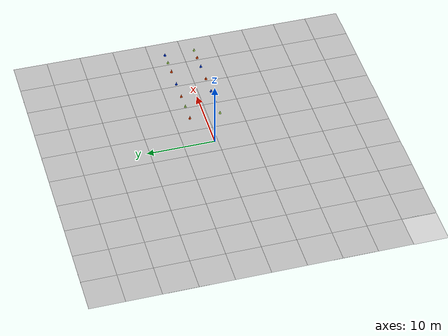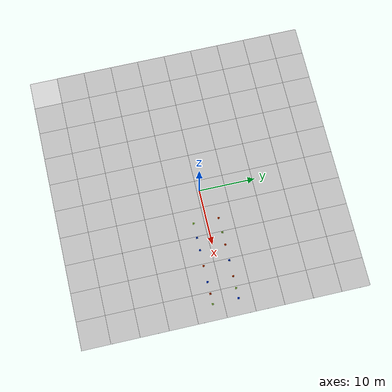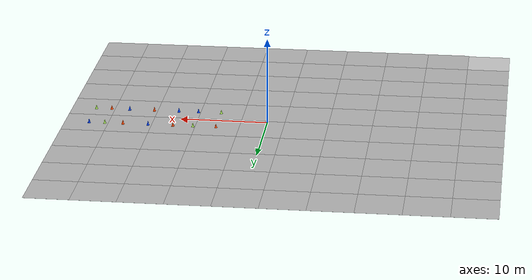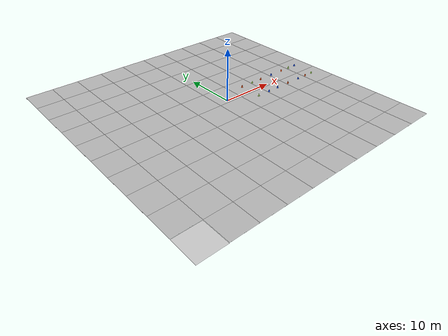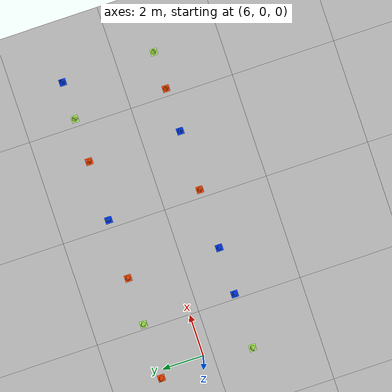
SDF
<sdf version="1.7">
 <world name="obstacles.world">
  <light name="sun" type="directional">
   <pose>0 0 10 0 -0 0</pose>
   <diffuse>0.8 0.8 0.8 1</diffuse>
   <specular>0.2 0.2 0.2 1</specular>
   <attenuation>
    <range>1000</range>
    <constant>0.9</constant>
    <linear>0.01</linear>
    <quadratic>0.001</quadratic>
   </attenuation>
   <direction>-0.5 0.1 -0.9</direction>
   <spot><inner_angle>0</inner_angle><outer_angle>0</outer_angle><falloff>0</falloff></spot>
  </light>
  <gravity>0 0 -9.8</gravity>
  <magnetic_field>6e-06 2.3e-05 -4.2e-05</magnetic_field>
  <atmosphere type="adiabatic"/>
  <physics type="ode">
   <max_step_size>0.001</max_step_size>
   <real_time_factor>1</real_time_factor>
   <real_time_update_rate>1000</real_time_update_rate>
  </physics>
  <scene><ambient>0.4 0.4 0.4 1</ambient><background>0.7 0.7 0.7 1</background><shadows>1</shadows></scene>
  <spherical_coordinates>
   <surface_model>EARTH_WGS84</surface_model>
   <latitude_deg>0</latitude_deg>
   <longitude_deg>0</longitude_deg>
   <elevation>0</elevation>
   <heading_deg>0</heading_deg>
  </spherical_coordinates>
  <model name="my_bot">
   <link name="base_link">
    <inertial>
     <pose>0.078466 -0.000667 0.041672 0 -0 0</pose>
     <mass>0.90002</mass>
     <inertia>
      <ixx>0.00658185</ixx>
      <ixy>-0.000163557</ixy>
      <ixz>2.47327e-05</ixz>
      <iyy>0.0100854</iyy>
      <iyz>-2.49866e-05</iyz>
      <izz>0.0118767</izz>
     </inertia>
    </inertial>
    <collision name="base_link_fixed_joint_lump__back_left_wheel_collision">
     <pose>0 0.085 0 -1.5708 0 0</pose>
     <geometry><cylinder><length>0.03</length><radius>0.032</radius></cylinder></geometry>
     <surface><friction><ode><mu>0.018</mu><mu2>0.018</mu2></ode></friction></surface>
    </collision>
    <collision name="base_link_fixed_joint_lump__back_right_wheel_collision_1">
     <pose>-0.0128 -0.091 0 1.5708 -0 0</pose>
     <geometry><cylinder><length>0.03</length><radius>0.032</radius></cylinder></geometry>
     <surface><friction><ode><mu>0.018</mu><mu2>0.018</mu2></ode></friction></surface>
    </collision>
    <collision name="base_link_fixed_joint_lump__camera_link_collision_2">
     <pose>0.16 -0.004 0.4572 0 -0 0</pose>
     <geometry><box><size>0.05 0.05 0.05</size></box></geometry>
    </collision>
    <collision name="base_link_fixed_joint_lump__chassis_collision_3">
     <pose>0.0778 0 0.075 0 -0 0</pose>
     <geometry><box><size>0.3302 0.1524 0.15</size></box></geometry>
    </collision>
    <collision name="base_link_fixed_joint_lump__front_left_wheel_collision_4">
     <pose>0.165 0.091 0 -1.5708 0 0</pose>
     <geometry><cylinder><length>0.03</length><radius>0.032</radius></cylinder></geometry>
     <surface><friction><ode><mu>0.018</mu><mu2>0.018</mu2></ode></friction></surface>
    </collision>
    <collision name="base_link_fixed_joint_lump__front_right_wheel_collision_5">
     <pose>0.165 -0.091 0 1.5708 -0 0</pose>
     <geometry><cylinder><length>0.03</length><radius>0.032</radius></cylinder></geometry>
     <surface><friction><ode><mu>0.018</mu><mu2>0.018</mu2></ode></friction></surface>
    </collision>
    <collision name="base_link_fixed_joint_lump__laser_frame_collision_6">
     <pose>-0.02 0 0.1143 0 -0 0</pose>
     <geometry><box><size>0.1 0.1 0.1</size></box></geometry>
    </collision>
    <visual name="base_link_fixed_joint_lump__back_left_wheel_visual">
     <pose>0 0.085 0 -1.5708 0 0</pose>
     <geometry><cylinder><length>0.03</length><radius>0.032</radius></cylinder></geometry>
     <material>
      <script><name>Gazebo/Blue</name><uri>file://media/materials/scripts/gazebo.material</uri></script>
     </material>
    </visual>
    <visual name="base_link_fixed_joint_lump__back_right_wheel_visual_1">
     <pose>-0.0128 -0.091 0 1.5708 -0 0</pose>
     <geometry><cylinder><length>0.03</length><radius>0.032</radius></cylinder></geometry>
     <material>
      <script><name>Gazebo/Blue</name><uri>file://media/materials/scripts/gazebo.material</uri></script>
     </material>
    </visual>
    <visual name="base_link_fixed_joint_lump__camera_link_visual_2">
     <pose>0.08 -0.002 0.2286 0 -0 0</pose>
     <geometry><box><size>0.05 0.05 0.05</size></box></geometry>
     <material>
      <script><name>Gazebo/Red</name><uri>file://media/materials/scripts/gazebo.material</uri></script>
     </material>
    </visual>
    <visual name="base_link_fixed_joint_lump__chassis_visual_3">
     <pose>0.0778 0 0.075 0 -0 0</pose>
     <geometry><box><size>0.3302 0.1524 0.15</size></box></geometry>
     <material>
      <script><name>Gazebo/Black</name><uri>file://media/materials/scripts/gazebo.material</uri></script>
     </material>
    </visual>
    <visual name="base_link_fixed_joint_lump__front_left_wheel_visual_4">
     <pose>0.165 0.091 0 -1.5708 0 0</pose>
     <geometry><cylinder><length>0.03</length><radius>0.032</radius></cylinder></geometry>
     <material>
      <script><name>Gazebo/Blue</name><uri>file://media/materials/scripts/gazebo.material</uri></script>
     </material>
    </visual>
    <visual name="base_link_fixed_joint_lump__front_right_wheel_visual_5">
     <pose>0.165 -0.091 0 1.5708 -0 0</pose>
     <geometry><cylinder><length>0.03</length><radius>0.032</radius></cylinder></geometry>
     <material>
      <script><name>Gazebo/Blue</name><uri>file://media/materials/scripts/gazebo.material</uri></script>
     </material>
    </visual>
    <visual name="base_link_fixed_joint_lump__laser_frame_visual_6">
     <pose>-0.02 0 0.1143 0 -0 0</pose>
     <geometry><box><size>0.06 0.05 0.05</size></box></geometry>
    </visual>
    <sensor name="camera1" type="camera">
     <update_rate>30</update_rate>
     <camera name="head">
      <horizontal_fov>1.0856</horizontal_fov>
      <image><width>3280</width><height>2464</height><format>R8G8B8</format></image>
      <clip><near>0.02</near><far>300</far></clip>
      <noise><type>gaussian</type><mean>0</mean><stddev>0.007</stddev></noise>
     </camera>
     <plugin name="camera_controller" filename="libgazebo_ros_camera.so">
      <alwaysOn>1</alwaysOn>
      <updateRate>0.0</updateRate>
      <cameraName>camera1</cameraName>
      <imageTopicName>image_raw</imageTopicName>
      <cameraInfoTopicName>camera_info</cameraInfoTopicName>
      <frameName>camera_link</frameName>
      <hackBaseline>0.07</hackBaseline>
      <distortionK1>0.0</distortionK1>
      <distortionK2>0.0</distortionK2>
      <distortionK3>0.0</distortionK3>
      <distortionT1>0.0</distortionT1>
      <distortionT2>0.0</distortionT2>
     </plugin>
     <pose>0.08 -0.002 0.2286 0 -0 0</pose>
    </sensor>
    <sensor name="laser" type="ray">
     <visualize>1</visualize>
     <update_rate>10</update_rate>
     <ray>
      <scan>
       <horizontal>
        <samples>90</samples>
        <resolution>10</resolution>
        <min_angle>-1.5708</min_angle>
        <max_angle>1.5708</max_angle>
       </horizontal>
       <vertical><samples>1</samples><min_angle>0</min_angle><max_angle>0</max_angle></vertical>
      </scan>
      <range><min>0.3</min><max>5</max><resolution>0.01</resolution></range>
     </ray>
     <plugin name="laser_controller" filename="libgazebo_ros_ray_sensor.so">
      <ros><argument>~/out:=scan</argument></ros>
      <output_type>sensor_msgs/LaserScan</output_type>
      <frame_name>laser_frame</frame_name>
     </plugin>
     <pose>-0.02 0 0.1143 0 -0 0</pose>
    </sensor>
   </link>
   <static>0</static>
   <plugin name="object_controller" filename="libgazebo_ros_planar_move.so">
    <commandTopic>cmd_vel</commandTopic>
    <odometryTopic>odom</odometryTopic>
    <odometryFrame>odom</odometryFrame>
    <odometryRate>20.0</odometryRate>
    <robot_base_frame>base_link</robot_base_frame>
   </plugin>
   <pose>-3e-06 2.1e-05 0.032 0 -0 -2.3e-05</pose>
  </model>
  <model name="blue_cone">
   <link name="link">
    <inertial>
     <pose>0 0.1 0 0 -0 0</pose>
     <mass>1</mass>
     <inertia><ixx>0.1</ixx><iyy>0.1</iyy><izz>0</izz><ixy>0</ixy><ixz>0</ixz><iyz>0</iyz></inertia>
    </inertial>
    <pose>-0.104311 -0.990632 5.9e-05 0 -0 0</pose>
    <visual name="visual">
     <geometry><mesh><scale>1 1 1</scale><uri>file://model.dae</uri></mesh></geometry>
     <material>
      <shader type="pixel"><normal_map>__default__</normal_map></shader>
      <script><name>ModelPreview_1::link::visual_MATERIAL_</name><uri>__default__</uri></script>
      <ambient>0 0.251 1 0</ambient>
      <diffuse>0 0.251 1 1</diffuse>
      <specular>0 0 0 1</specular>
      <emissive>0 0 0 1</emissive>
     </material>
    </visual>
    <collision name="collision">
     <geometry>
      <mesh>
       <uri>/home/josh/robot_ws/src/open-source-autonomous-vehicle-controller/car_ros/worlds/model.dae</uri>
       <scale>1 1 1</scale>
      </mesh>
     </geometry>
     <surface>
      <friction>
       <ode><mu>1</mu><mu2>1</mu2><fdir1>0 0 0</fdir1><slip1>0</slip1><slip2>0</slip2></ode>
       <torsional>
        <coefficient>1</coefficient>
        <patch_radius>0</patch_radius>
        <surface_radius>0</surface_radius>
        <use_patch_radius>1</use_patch_radius>
        <ode><slip>0</slip></ode>
       </torsional>
      </friction>
      <bounce><restitution_coefficient>0</restitution_coefficient><threshold>1e+06</threshold></bounce>
      <contact>
       <collide_without_contact>0</collide_without_contact>
       <collide_without_contact_bitmask>1</collide_without_contact_bitmask>
       <collide_bitmask>1</collide_bitmask>
       <ode>
        <soft_cfm>0</soft_cfm>
        <soft_erp>0.2</soft_erp>
        <kp>1e+13</kp>
        <kd>1</kd>
        <max_vel>0.01</max_vel>
        <min_depth>0</min_depth>
       </ode>
       <bullet>
        <split_impulse>1</split_impulse>
        <split_impulse_penetration_threshold>-0.01</split_impulse_penetration_threshold>
        <soft_cfm>0</soft_cfm>
        <soft_erp>0.2</soft_erp>
        <kp>1e+13</kp>
        <kd>1</kd>
       </bullet>
      </contact>
     </surface>
    </collision>
    <static>1</static>
   </link>
   <static>0</static>
   <pose>8.21378 -1.47102 -2e-06 -1e-06 -0.000562 0</pose>
  </model>
  <model name="orange_cone">
   <link name="link">
    <inertial>
     <pose>0 0.1 0 0 -0 0</pose>
     <mass>1</mass>
     <inertia><ixx>0.1</ixx><iyy>0.1</iyy><izz>0</izz><ixy>0</ixy><ixz>0</ixz><iyz>0</iyz></inertia>
    </inertial>
    <pose>-0.104311 -0.990632 5.9e-05 0 -0 0</pose>
    <visual name="visual">
     <geometry><mesh><scale>1 1 1</scale><uri>file://model.dae</uri></mesh></geometry>
     <material>
      <shader type="pixel"><normal_map>__default__</normal_map></shader>
      <script><name>ModelPreview_1::link::visual_MATERIAL_</name><uri>__default__</uri></script>
      <ambient>1 0.271 0 0</ambient>
      <diffuse>1 0.271 0 1</diffuse>
      <specular>0 0 0 1</specular>
      <emissive>0 0 0 1</emissive>
     </material>
    </visual>
    <collision name="collision">
     <geometry>
      <mesh>
       <uri>/home/josh/robot_ws/src/open-source-autonomous-vehicle-controller/car_ros/worlds/model.dae</uri>
       <scale>1 1 1</scale>
      </mesh>
     </geometry>
     <surface>
      <friction>
       <ode><mu>1</mu><mu2>1</mu2><fdir1>0 0 0</fdir1><slip1>0</slip1><slip2>0</slip2></ode>
       <torsional>
        <coefficient>1</coefficient>
        <patch_radius>0</patch_radius>
        <surface_radius>0</surface_radius>
        <use_patch_radius>1</use_patch_radius>
        <ode><slip>0</slip></ode>
       </torsional>
      </friction>
      <bounce><restitution_coefficient>0</restitution_coefficient><threshold>1e+06</threshold></bounce>
      <contact>
       <collide_without_contact>0</collide_without_contact>
       <collide_without_contact_bitmask>1</collide_without_contact_bitmask>
       <collide_bitmask>1</collide_bitmask>
       <ode>
        <soft_cfm>0</soft_cfm>
        <soft_erp>0.2</soft_erp>
        <kp>1e+13</kp>
        <kd>1</kd>
        <max_vel>0.01</max_vel>
        <min_depth>0</min_depth>
       </ode>
       <bullet>
        <split_impulse>1</split_impulse>
        <split_impulse_penetration_threshold>-0.01</split_impulse_penetration_threshold>
        <soft_cfm>0</soft_cfm>
        <soft_erp>0.2</soft_erp>
        <kp>1e+13</kp>
        <kd>1</kd>
       </bullet>
      </contact>
     </surface>
    </collision>
    <static>1</static>
   </link>
   <static>0</static>
   <pose>5.56633 3.02032 -2e-06 -1e-06 -0.000562 0</pose>
  </model>
  <model name="neon_cone">
   <link name="link">
    <inertial>
     <pose>0 0.1 0 0 -0 0</pose>
     <mass>1</mass>
     <inertia><ixx>0.1</ixx><iyy>0.1</iyy><izz>0</izz><ixy>0</ixy><ixz>0</ixz><iyz>0</iyz></inertia>
    </inertial>
    <pose>-0.104311 -0.990632 5.9e-05 0 -0 0</pose>
    <visual name="visual">
     <geometry><mesh><scale>1 1 1</scale><uri>file://model.dae</uri></mesh></geometry>
     <material>
      <shader type="pixel"><normal_map>__default__</normal_map></shader>
      <script><name>ModelPreview_1::link::visual_MATERIAL_</name><uri>__default__</uri></script>
      <ambient>0.682 0.953 0.349 0</ambient>
      <diffuse>0.682 0.953 0.349 1</diffuse>
      <specular>0 0 0 1</specular>
      <emissive>0 0 0 1</emissive>
     </material>
    </visual>
    <collision name="collision">
     <geometry>
      <mesh>
       <uri>/home/josh/robot_ws/src/open-source-autonomous-vehicle-controller/car_ros/worlds/model.dae</uri>
       <scale>1 1 1</scale>
      </mesh>
     </geometry>
     <surface>
      <friction>
       <ode><mu>1</mu><mu2>1</mu2><fdir1>0 0 0</fdir1><slip1>0</slip1><slip2>0</slip2></ode>
       <torsional>
        <coefficient>1</coefficient>
        <patch_radius>0</patch_radius>
        <surface_radius>0</surface_radius>
        <use_patch_radius>1</use_patch_radius>
        <ode><slip>0</slip></ode>
       </torsional>
      </friction>
      <bounce><restitution_coefficient>0</restitution_coefficient><threshold>1e+06</threshold></bounce>
      <contact>
       <collide_without_contact>0</collide_without_contact>
       <collide_without_contact_bitmask>1</collide_without_contact_bitmask>
       <collide_bitmask>1</collide_bitmask>
       <ode>
        <soft_cfm>0</soft_cfm>
        <soft_erp>0.2</soft_erp>
        <kp>1e+13</kp>
        <kd>1</kd>
        <max_vel>0.01</max_vel>
        <min_depth>0</min_depth>
       </ode>
       <bullet>
        <split_impulse>1</split_impulse>
        <split_impulse_penetration_threshold>-0.01</split_impulse_penetration_threshold>
        <soft_cfm>0</soft_cfm>
        <soft_erp>0.2</soft_erp>
        <kp>1e+13</kp>
        <kd>1</kd>
       </bullet>
      </contact>
     </surface>
    </collision>
    <static>1</static>
   </link>
   <static>0</static>
   <pose>5.56633 -1.47102 -2e-06 -1e-06 -0.000562 0</pose>
  </model>
  <model name="pavement_plane">
   <static>1</static>
   <link name="link">
    <collision name="collision">
     <geometry><plane><normal>0 0 1</normal><size>50 50</size></plane></geometry>
     <surface><friction><ode><mu>100</mu><mu2>50</mu2></ode></friction></surface>
    </collision>
    <visual name="visual_0">
     <pose>-25 -25 0 0 -0 0</pose>
     <cast_shadows>0</cast_shadows>
     <geometry><plane><normal>0 0 1</normal><size>5 5</size></plane></geometry>
     <material>
      <script>
       <uri>https://fuel.ignitionrobotics.org/1.0/openrobotics/models/pavement plane/1/files/materials/scripts</uri>
       <uri>https://fuel.ignitionrobotics.org/1.0/openrobotics/models/pavement plane/1/files/materials/textures</uri>
       <name>vrc/pavement</name>
      </script>
     </material>
    </visual>
    <visual name="visual_1">
     <pose>-20 -25 0 0 -0 0</pose>
     <cast_shadows>0</cast_shadows>
     <geometry><plane><normal>0 0 1</normal><size>5 5</size></plane></geometry>
     <material>
      <script>
       <uri>https://fuel.ignitionrobotics.org/1.0/openrobotics/models/pavement plane/1/files/materials/scripts</uri>
       <uri>https://fuel.ignitionrobotics.org/1.0/openrobotics/models/pavement plane/1/files/materials/textures</uri>
       <name>vrc/pavement</name>
      </script>
     </material>
    </visual>
    <visual name="visual_2">
     <pose>-15 -25 0 0 -0 0</pose>
     <cast_shadows>0</cast_shadows>
     <geometry><plane><normal>0 0 1</normal><size>5 5</size></plane></geometry>
     <material>
      <script>
       <uri>https://fuel.ignitionrobotics.org/1.0/openrobotics/models/pavement plane/1/files/materials/scripts</uri>
       <uri>https://fuel.ignitionrobotics.org/1.0/openrobotics/models/pavement plane/1/files/materials/textures</uri>
       <name>vrc/pavement</name>
      </script>
     </material>
    </visual>
    <visual name="visual_3">
     <pose>-10 -25 0 0 -0 0</pose>
     <cast_shadows>0</cast_shadows>
     <geometry><plane><normal>0 0 1</normal><size>5 5</size></plane></geometry>
     <material>
      <script>
       <uri>https://fuel.ignitionrobotics.org/1.0/openrobotics/models/pavement plane/1/files/materials/scripts</uri>
       <uri>https://fuel.ignitionrobotics.org/1.0/openrobotics/models/pavement plane/1/files/materials/textures</uri>
       <name>vrc/pavement</name>
      </script>
     </material>
    </visual>
    <visual name="visual_4">
     <pose>-5 -25 0 0 -0 0</pose>
     <cast_shadows>0</cast_shadows>
     <geometry><plane><normal>0 0 1</normal><size>5 5</size></plane></geometry>
     <material>
      <script>
       <uri>https://fuel.ignitionrobotics.org/1.0/openrobotics/models/pavement plane/1/files/materials/scripts</uri>
       <uri>https://fuel.ignitionrobotics.org/1.0/openrobotics/models/pavement plane/1/files/materials/textures</uri>
       <name>vrc/pavement</name>
      </script>
     </material>
    </visual>
    <visual name="visual_5">
     <pose>0 -25 0 0 -0 0</pose>
     <cast_shadows>0</cast_shadows>
     <geometry><plane><normal>0 0 1</normal><size>5 5</size></plane></geometry>
     <material>
      <script>
       <uri>https://fuel.ignitionrobotics.org/1.0/openrobotics/models/pavement plane/1/files/materials/scripts</uri>
       <uri>https://fuel.ignitionrobotics.org/1.0/openrobotics/models/pavement plane/1/files/materials/textures</uri>
       <name>vrc/pavement</name>
      </script>
     </material>
    </visual>
    <visual name="visual_6">
     <pose>5 -25 0 0 -0 0</pose>
     <cast_shadows>0</cast_shadows>
     <geometry><plane><normal>0 0 1</normal><size>5 5</size></plane></geometry>
     <material>
      <script>
       <uri>https://fuel.ignitionrobotics.org/1.0/openrobotics/models/pavement plane/1/files/materials/scripts</uri>
       <uri>https://fuel.ignitionrobotics.org/1.0/openrobotics/models/pavement plane/1/files/materials/textures</uri>
       <name>vrc/pavement</name>
      </script>
     </material>
    </visual>
    <visual name="visual_7">
     <pose>10 -25 0 0 -0 0</pose>
     <cast_shadows>0</cast_shadows>
     <geometry><plane><normal>0 0 1</normal><size>5 5</size></plane></geometry>
     <material>
      <script>
       <uri>https://fuel.ignitionrobotics.org/1.0/openrobotics/models/pavement plane/1/files/materials/scripts</uri>
       <uri>https://fuel.ignitionrobotics.org/1.0/openrobotics/models/pavement plane/1/files/materials/textures</uri>
       <name>vrc/pavement</name>
      </script>
     </material>
    </visual>
    <visual name="visual_8">
     <pose>15 -25 0 0 -0 0</pose>
     <cast_shadows>0</cast_shadows>
     <geometry><plane><normal>0 0 1</normal><size>5 5</size></plane></geometry>
     <material>
      <script>
       <uri>https://fuel.ignitionrobotics.org/1.0/openrobotics/models/pavement plane/1/files/materials/scripts</uri>
       <uri>https://fuel.ignitionrobotics.org/1.0/openrobotics/models/pavement plane/1/files/materials/textures</uri>
       <name>vrc/pavement</name>
      </script>
     </material>
    </visual>
    <visual name="visual_9">
     <pose>20 -25 0 0 -0 0</pose>
     <cast_shadows>0</cast_shadows>
     <geometry><plane><normal>0 0 1</normal><size>5 5</size></plane></geometry>
     <material>
      <script>
       <uri>https://fuel.ignitionrobotics.org/1.0/openrobotics/models/pavement plane/1/files/materials/scripts</uri>
       <uri>https://fuel.ignitionrobotics.org/1.0/openrobotics/models/pavement plane/1/files/materials/textures</uri>
       <name>vrc/pavement</name>
      </script>
     </material>
    </visual>
    <visual name="visual_10">
     <pose>-25 -20 0 0 -0 0</pose>
     <cast_shadows>0</cast_shadows>
     <geometry><plane><normal>0 0 1</normal><size>5 5</size></plane></geometry>
     <material>
      <script>
       <uri>https://fuel.ignitionrobotics.org/1.0/openrobotics/models/pavement plane/1/files/materials/scripts</uri>
       <uri>https://fuel.ignitionrobotics.org/1.0/openrobotics/models/pavement plane/1/files/materials/textures</uri>
       <name>vrc/pavement</name>
      </script>
     </material>
    </visual>
    <visual name="visual_11">
     <pose>-20 -20 0 0 -0 0</pose>
     <cast_shadows>0</cast_shadows>
     <geometry><plane><normal>0 0 1</normal><size>5 5</size></plane></geometry>
     <material>
      <script>
       <uri>https://fuel.ignitionrobotics.org/1.0/openrobotics/models/pavement plane/1/files/materials/scripts</uri>
       <uri>https://fuel.ignitionrobotics.org/1.0/openrobotics/models/pavement plane/1/files/materials/textures</uri>
       <name>vrc/pavement</name>
      </script>
     </material>
    </visual>
    <visual name="visual_12">
     <pose>-15 -20 0 0 -0 0</pose>
     <cast_shadows>0</cast_shadows>
     <geometry><plane><normal>0 0 1</normal><size>5 5</size></plane></geometry>
     <material>
      <script>
       <uri>https://fuel.ignitionrobotics.org/1.0/openrobotics/models/pavement plane/1/files/materials/scripts</uri>
       <uri>https://fuel.ignitionrobotics.org/1.0/openrobotics/models/pavement plane/1/files/materials/textures</uri>
       <name>vrc/pavement</name>
      </script>
     </material>
    </visual>
    <visual name="visual_13">
     <pose>-10 -20 0 0 -0 0</pose>
     <cast_shadows>0</cast_shadows>
     <geometry><plane><normal>0 0 1</normal><size>5 5</size></plane></geometry>
     <material>
      <script>
       <uri>https://fuel.ignitionrobotics.org/1.0/openrobotics/models/pavement plane/1/files/materials/scripts</uri>
       <uri>https://fuel.ignitionrobotics.org/1.0/openrobotics/models/pavement plane/1/files/materials/textures</uri>
       <name>vrc/pavement</name>
      </script>
     </material>
    </visual>
    <visual name="visual_14">
     <pose>-5 -20 0 0 -0 0</pose>
     <cast_shadows>0</cast_shadows>
     <geometry><plane><normal>0 0 1</normal><size>5 5</size></plane></geometry>
     <material>
      <script>
       <uri>https://fuel.ignitionrobotics.org/1.0/openrobotics/models/pavement plane/1/files/materials/scripts</uri>
       <uri>https://fuel.ignitionrobotics.org/1.0/openrobotics/models/pavement plane/1/files/materials/textures</uri>
       <name>vrc/pavement</name>
      </script>
     </material>
    </visual>
    <visual name="visual_15">
     <pose>0 -20 0 0 -0 0</pose>
     <cast_shadows>0</cast_shadows>
     <geometry><plane><normal>0 0 1</normal><size>5 5</size></plane></geometry>
     <material>
      <script>
       <uri>https://fuel.ignitionrobotics.org/1.0/openrobotics/models/pavement plane/1/files/materials/scripts</uri>
       <uri>https://fuel.ignitionrobotics.org/1.0/openrobotics/models/pavement plane/1/files/materials/textures</uri>
       <name>vrc/pavement</name>
      </script>
     </material>
    </visual>
    <visual name="visual_16">
     <pose>5 -20 0 0 -0 0</pose>
     <cast_shadows>0</cast_shadows>
     <geometry><plane><normal>0 0 1</normal><size>5 5</size></plane></geometry>
     <material>
      <script>
       <uri>https://fuel.ignitionrobotics.org/1.0/openrobotics/models/pavement plane/1/files/materials/scripts</uri>
       <uri>https://fuel.ignitionrobotics.org/1.0/openrobotics/models/pavement plane/1/files/materials/textures</uri>
       <name>vrc/pavement</name>
      </script>
     </material>
    </visual>
    <visual name="visual_17">
     <pose>10 -20 0 0 -0 0</pose>
     <cast_shadows>0</cast_shadows>
     <geometry><plane><normal>0 0 1</normal><size>5 5</size></plane></geometry>
     <material>
      <script>
       <uri>https://fuel.ignitionrobotics.org/1.0/openrobotics/models/pavement plane/1/files/materials/scripts</uri>
       <uri>https://fuel.ignitionrobotics.org/1.0/openrobotics/models/pavement plane/1/files/materials/textures</uri>
       <name>vrc/pavement</name>
      </script>
     </material>
    </visual>
    <visual name="visual_18">
     <pose>15 -20 0 0 -0 0</pose>
     <cast_shadows>0</cast_shadows>
     <geometry><plane><normal>0 0 1</normal><size>5 5</size></plane></geometry>
     <material>
      <script>
       <uri>https://fuel.ignitionrobotics.org/1.0/openrobotics/models/pavement plane/1/files/materials/scripts</uri>
       <uri>https://fuel.ignitionrobotics.org/1.0/openrobotics/models/pavement plane/1/files/materials/textures</uri>
       <name>vrc/pavement</name>
      </script>
     </material>
    </visual>
    <visual name="visual_19">
     <pose>20 -20 0 0 -0 0</pose>
     <cast_shadows>0</cast_shadows>
     <geometry><plane><normal>0 0 1</normal><size>5 5</size></plane></geometry>
     <material>
      <script>
       <uri>https://fuel.ignitionrobotics.org/1.0/openrobotics/models/pavement plane/1/files/materials/scripts</uri>
       <uri>https://fuel.ignitionrobotics.org/1.0/openrobotics/models/pavement plane/1/files/materials/textures</uri>
       <name>vrc/pavement</name>
      </script>
     </material>
    </visual>
    <visual name="visual_20">
     <pose>-25 -15 0 0 -0 0</pose>
     <cast_shadows>0</cast_shadows>
     <geometry><plane><normal>0 0 1</normal><size>5 5</size></plane></geometry>
     <material>
      <script>
       <uri>https://fuel.ignitionrobotics.org/1.0/openrobotics/models/pavement plane/1/files/materials/scripts</uri>
       <uri>https://fuel.ignitionrobotics.org/1.0/openrobotics/models/pavement plane/1/files/materials/textures</uri>
       <name>vrc/pavement</name>
      </script>
     </material>
    </visual>
    <visual name="visual_21">
     <pose>-20 -15 0 0 -0 0</pose>
     <cast_shadows>0</cast_shadows>
     <geometry><plane><normal>0 0 1</normal><size>5 5</size></plane></geometry>
     <material>
      <script>
       <uri>https://fuel.ignitionrobotics.org/1.0/openrobotics/models/pavement plane/1/files/materials/scripts</uri>
       <uri>https://fuel.ignitionrobotics.org/1.0/openrobotics/models/pavement plane/1/files/materials/textures</uri>
       <name>vrc/pavement</name>
      </script>
     </material>
    </visual>
    <visual name="visual_22">
     <pose>-15 -15 0 0 -0 0</pose>
     <cast_shadows>0</cast_shadows>
     <geometry><plane><normal>0 0 1</normal><size>5 5</size></plane></geometry>
     <material>
      <script>
       <uri>https://fuel.ignitionrobotics.org/1.0/openrobotics/models/pavement plane/1/files/materials/scripts</uri>
       <uri>https://fuel.ignitionrobotics.org/1.0/openrobotics/models/pavement plane/1/files/materials/textures</uri>
       <name>vrc/pavement</name>
      </script>
     </material>
    </visual>
    <visual name="visual_23">
     <pose>-10 -15 0 0 -0 0</pose>
     <cast_shadows>0</cast_shadows>
     <geometry><plane><normal>0 0 1</normal><size>5 5</size></plane></geometry>
     <material>
      <script>
       <uri>https://fuel.ignitionrobotics.org/1.0/openrobotics/models/pavement plane/1/files/materials/scripts</uri>
       <uri>https://fuel.ignitionrobotics.org/1.0/openrobotics/models/pavement plane/1/files/materials/textures</uri>
       <name>vrc/pavement</name>
      </script>
     </material>
    </visual>
    <visual name="visual_24">
     <pose>-5 -15 0 0 -0 0</pose>
     <cast_shadows>0</cast_shadows>
     <geometry><plane><normal>0 0 1</normal><size>5 5</size></plane></geometry>
     <material>
      <script>
       <uri>https://fuel.ignitionrobotics.org/1.0/openrobotics/models/pavement plane/1/files/materials/scripts</uri>
       <uri>https://fuel.ignitionrobotics.org/1.0/openrobotics/models/pavement plane/1/files/materials/textures</uri>
       <name>vrc/pavement</name>
      </script>
     </material>
    </visual>
    <visual name="visual_25">
     <pose>0 -15 0 0 -0 0</pose>
     <cast_shadows>0</cast_shadows>
     <geometry><plane><normal>0 0 1</normal><size>5 5</size></plane></geometry>
     <material>
      <script>
       <uri>https://fuel.ignitionrobotics.org/1.0/openrobotics/models/pavement plane/1/files/materials/scripts</uri>
       <uri>https://fuel.ignitionrobotics.org/1.0/openrobotics/models/pavement plane/1/files/materials/textures</uri>
       <name>vrc/pavement</name>
      </script>
     </material>
    </visual>
    <visual name="visual_26">
     <pose>5 -15 0 0 -0 0</pose>
     <cast_shadows>0</cast_shadows>
     <geometry><plane><normal>0 0 1</normal><size>5 5</size></plane></geometry>
     <material>
      <script>
       <uri>https://fuel.ignitionrobotics.org/1.0/openrobotics/models/pavement plane/1/files/materials/scripts</uri>
       <uri>https://fuel.ignitionrobotics.org/1.0/openrobotics/models/pavement plane/1/files/materials/textures</uri>
       <name>vrc/pavement</name>
      </script>
     </material>
    </visual>
    <visual name="visual_27">
     <pose>10 -15 0 0 -0 0</pose>
     <cast_shadows>0</cast_shadows>
     <geometry><plane><normal>0 0 1</normal><size>5 5</size></plane></geometry>
     <material>
      <script>
       <uri>https://fuel.ignitionrobotics.org/1.0/openrobotics/models/pavement plane/1/files/materials/scripts</uri>
       <uri>https://fuel.ignitionrobotics.org/1.0/openrobotics/models/pavement plane/1/files/materials/textures</uri>
       <name>vrc/pavement</name>
      </script>
     </material>
    </visual>
    <visual name="visual_28">
     <pose>15 -15 0 0 -0 0</pose>
     <cast_shadows>0</cast_shadows>
     <geometry><plane><normal>0 0 1</normal><size>5 5</size></plane></geometry>
     <material>
      <script>
       <uri>https://fuel.ignitionrobotics.org/1.0/openrobotics/models/pavement plane/1/files/materials/scripts</uri>
       <uri>https://fuel.ignitionrobotics.org/1.0/openrobotics/models/pavement plane/1/files/materials/textures</uri>
       <name>vrc/pavement</name>
      </script>
     </material>
    </visual>
    <visual name="visual_29">
     <pose>20 -15 0 0 -0 0</pose>
     <cast_shadows>0</cast_shadows>
     <geometry><plane><normal>0 0 1</normal><size>5 5</size></plane></geometry>
     <material>
      <script>
       <uri>https://fuel.ignitionrobotics.org/1.0/openrobotics/models/pavement plane/1/files/materials/scripts</uri>
       <uri>https://fuel.ignitionrobotics.org/1.0/openrobotics/models/pavement plane/1/files/materials/textures</uri>
       <name>vrc/pavement</name>
      </script>
     </material>
    </visual>
    <visual name="visual_30">
     <pose>-25 -10 0 0 -0 0</pose>
     <cast_shadows>0</cast_shadows>
     <geometry><plane><normal>0 0 1</normal><size>5 5</size></plane></geometry>
     <material>
      <script>
       <uri>https://fuel.ignitionrobotics.org/1.0/openrobotics/models/pavement plane/1/files/materials/scripts</uri>
       <uri>https://fuel.ignitionrobotics.org/1.0/openrobotics/models/pavement plane/1/files/materials/textures</uri>
       <name>vrc/pavement</name>
      </script>
     </material>
    </visual>
    <visual name="visual_31">
     <pose>-20 -10 0 0 -0 0</pose>
     <cast_shadows>0</cast_shadows>
     <geometry><plane><normal>0 0 1</normal><size>5 5</size></plane></geometry>
     <material>
      <script>
       <uri>https://fuel.ignitionrobotics.org/1.0/openrobotics/models/pavement plane/1/files/materials/scripts</uri>
       <uri>https://fuel.ignitionrobotics.org/1.0/openrobotics/models/pavement plane/1/files/materials/textures</uri>
       <name>vrc/pavement</name>
      </script>
     </material>
    </visual>
    <visual name="visual_32">
     <pose>-15 -10 0 0 -0 0</pose>
     <cast_shadows>0</cast_shadows>
     <geometry><plane><normal>0 0 1</normal><size>5 5</size></plane></geometry>
     <material>
      <script>
       <uri>https://fuel.ignitionrobotics.org/1.0/openrobotics/models/pavement plane/1/files/materials/scripts</uri>
       <uri>https://fuel.ignitionrobotics.org/1.0/openrobotics/models/pavement plane/1/files/materials/textures</uri>
       <name>vrc/pavement</name>
      </script>
     </material>
    </visual>
    <visual name="visual_33">
     <pose>-10 -10 0 0 -0 0</pose>
     <cast_shadows>0</cast_shadows>
     <geometry><plane><normal>0 0 1</normal><size>5 5</size></plane></geometry>
     <material>
      <script>
       <uri>https://fuel.ignitionrobotics.org/1.0/openrobotics/models/pavement plane/1/files/materials/scripts</uri>
       <uri>https://fuel.ignitionrobotics.org/1.0/openrobotics/models/pavement plane/1/files/materials/textures</uri>
       <name>vrc/pavement</name>
      </script>
     </material>
    </visual>
    <visual name="visual_34">
     <pose>-5 -10 0 0 -0 0</pose>
     <cast_shadows>0</cast_shadows>
     <geometry><plane><normal>0 0 1</normal><size>5 5</size></plane></geometry>
     <material>
      <script>
       <uri>https://fuel.ignitionrobotics.org/1.0/openrobotics/models/pavement plane/1/files/materials/scripts</uri>
       <uri>https://fuel.ignitionrobotics.org/1.0/openrobotics/models/pavement plane/1/files/materials/textures</uri>
       <name>vrc/pavement</name>
      </script>
     </material>
    </visual>
    <visual name="visual_35">
     <pose>0 -10 0 0 -0 0</pose>
     <cast_shadows>0</cast_shadows>
     <geometry><plane><normal>0 0 1</normal><size>5 5</size></plane></geometry>
     <material>
      <script>
       <uri>https://fuel.ignitionrobotics.org/1.0/openrobotics/models/pavement plane/1/files/materials/scripts</uri>
       <uri>https://fuel.ignitionrobotics.org/1.0/openrobotics/models/pavement plane/1/files/materials/textures</uri>
       <name>vrc/pavement</name>
      </script>
     </material>
    </visual>
    <visual name="visual_36">
     <pose>5 -10 0 0 -0 0</pose>
     <cast_shadows>0</cast_shadows>
     <geometry><plane><normal>0 0 1</normal><size>5 5</size></plane></geometry>
     <material>
      <script>
       <uri>https://fuel.ignitionrobotics.org/1.0/openrobotics/models/pavement plane/1/files/materials/scripts</uri>
       <uri>https://fuel.ignitionrobotics.org/1.0/openrobotics/models/pavement plane/1/files/materials/textures</uri>
       <name>vrc/pavement</name>
      </script>
     </material>
    </visual>
    <visual name="visual_37">
     <pose>10 -10 0 0 -0 0</pose>
     <cast_shadows>0</cast_shadows>
     <geometry><plane><normal>0 0 1</normal><size>5 5</size></plane></geometry>
     <material>
      <script>
       <uri>https://fuel.ignitionrobotics.org/1.0/openrobotics/models/pavement plane/1/files/materials/scripts</uri>
       <uri>https://fuel.ignitionrobotics.org/1.0/openrobotics/models/pavement plane/1/files/materials/textures</uri>
       <name>vrc/pavement</name>
      </script>
     </material>
    </visual>
    <visual name="visual_38">
     <pose>15 -10 0 0 -0 0</pose>
     <cast_shadows>0</cast_shadows>
     <geometry><plane><normal>0 0 1</normal><size>5 5</size></plane></geometry>
     <material>
      <script>
       <uri>https://fuel.ignitionrobotics.org/1.0/openrobotics/models/pavement plane/1/files/materials/scripts</uri>
       <uri>https://fuel.ignitionrobotics.org/1.0/openrobotics/models/pavement plane/1/files/materials/textures</uri>
       <name>vrc/pavement</name>
      </script>
     </material>
    </visual>
    <visual name="visual_39">
     <pose>20 -10 0 0 -0 0</pose>
     <cast_shadows>0</cast_shadows>
     <geometry><plane><normal>0 0 1</normal><size>5 5</size></plane></geometry>
     <material>
      <script>
       <uri>https://fuel.ignitionrobotics.org/1.0/openrobotics/models/pavement plane/1/files/materials/scripts</uri>
       <uri>https://fuel.ignitionrobotics.org/1.0/openrobotics/models/pavement plane/1/files/materials/textures</uri>
       <name>vrc/pavement</name>
      </script>
     </material>
    </visual>
    <visual name="visual_40">
     <pose>-25 -5 0 0 -0 0</pose>
     <cast_shadows>0</cast_shadows>
     <geometry><plane><normal>0 0 1</normal><size>5 5</size></plane></geometry>
     <material>
      <script>
       <uri>https://fuel.ignitionrobotics.org/1.0/openrobotics/models/pavement plane/1/files/materials/scripts</uri>
       <uri>https://fuel.ignitionrobotics.org/1.0/openrobotics/models/pavement plane/1/files/materials/textures</uri>
       <name>vrc/pavement</name>
      </script>
     </material>
    </visual>
    <visual name="visual_41">
     <pose>-20 -5 0 0 -0 0</pose>
     <cast_shadows>0</cast_shadows>
     <geometry><plane><normal>0 0 1</normal><size>5 5</size></plane></geometry>
     <material>
      <script>
       <uri>https://fuel.ignitionrobotics.org/1.0/openrobotics/models/pavement plane/1/files/materials/scripts</uri>
       <uri>https://fuel.ignitionrobotics.org/1.0/openrobotics/models/pavement plane/1/files/materials/textures</uri>
       <name>vrc/pavement</name>
      </script>
     </material>
    </visual>
    <visual name="visual_42">
     <pose>-15 -5 0 0 -0 0</pose>
     <cast_shadows>0</cast_shadows>
     <geometry><plane><normal>0 0 1</normal><size>5 5</size></plane></geometry>
     <material>
      <script>
       <uri>https://fuel.ignitionrobotics.org/1.0/openrobotics/models/pavement plane/1/files/materials/scripts</uri>
       <uri>https://fuel.ignitionrobotics.org/1.0/openrobotics/models/pavement plane/1/files/materials/textures</uri>
       <name>vrc/pavement</name>
      </script>
     </material>
    </visual>
    <visual name="visual_43">
     <pose>-10 -5 0 0 -0 0</pose>
     <cast_shadows>0</cast_shadows>
     <geometry><plane><normal>0 0 1</normal><size>5 5</size></plane></geometry>
     <material>
      <script>
       <uri>https://fuel.ignitionrobotics.org/1.0/openrobotics/models/pavement plane/1/files/materials/scripts</uri>
       <uri>https://fuel.ignitionrobotics.org/1.0/openrobotics/models/pavement plane/1/files/materials/textures</uri>
       <name>vrc/pavement</name>
      </script>
     </material>
    </visual>
    <visual name="visual_44">
     <pose>-5 -5 0 0 -0 0</pose>
     <cast_shadows>0</cast_shadows>
     <geometry><plane><normal>0 0 1</normal><size>5 5</size></plane></geometry>
     <material>
      <script>
       <uri>https://fuel.ignitionrobotics.org/1.0/openrobotics/models/pavement plane/1/files/materials/scripts</uri>
       <uri>https://fuel.ignitionrobotics.org/1.0/openrobotics/models/pavement plane/1/files/materials/textures</uri>
       <name>vrc/pavement</name>
      </script>
     </material>
    </visual>
    <visual name="visual_45">
     <pose>0 -5 0 0 -0 0</pose>
     <cast_shadows>0</cast_shadows>
     <geometry><plane><normal>0 0 1</normal><size>5 5</size></plane></geometry>
     <material>
      <script>
       <uri>https://fuel.ignitionrobotics.org/1.0/openrobotics/models/pavement plane/1/files/materials/scripts</uri>
       <uri>https://fuel.ignitionrobotics.org/1.0/openrobotics/models/pavement plane/1/files/materials/textures</uri>
       <name>vrc/pavement</name>
      </script>
     </material>
    </visual>
    <visual name="visual_46">
     <pose>5 -5 0 0 -0 0</pose>
     <cast_shadows>0</cast_shadows>
     <geometry><plane><normal>0 0 1</normal><size>5 5</size></plane></geometry>
     <material>
      <script>
       <uri>https://fuel.ignitionrobotics.org/1.0/openrobotics/models/pavement plane/1/files/materials/scripts</uri>
       <uri>https://fuel.ignitionrobotics.org/1.0/openrobotics/models/pavement plane/1/files/materials/textures</uri>
       <name>vrc/pavement</name>
      </script>
     </material>
    </visual>
    <visual name="visual_47">
     <pose>10 -5 0 0 -0 0</pose>
     <cast_shadows>0</cast_shadows>
     <geometry><plane><normal>0 0 1</normal><size>5 5</size></plane></geometry>
     <material>
      <script>
       <uri>https://fuel.ignitionrobotics.org/1.0/openrobotics/models/pavement plane/1/files/materials/scripts</uri>
       <uri>https://fuel.ignitionrobotics.org/1.0/openrobotics/models/pavement plane/1/files/materials/textures</uri>
       <name>vrc/pavement</name>
      </script>
     </material>
    </visual>
    <visual name="visual_48">
     <pose>15 -5 0 0 -0 0</pose>
     <cast_shadows>0</cast_shadows>
     <geometry><plane><normal>0 0 1</normal><size>5 5</size></plane></geometry>
     <material>
      <script>
       <uri>https://fuel.ignitionrobotics.org/1.0/openrobotics/models/pavement plane/1/files/materials/scripts</uri>
       <uri>https://fuel.ignitionrobotics.org/1.0/openrobotics/models/pavement plane/1/files/materials/textures</uri>
       <name>vrc/pavement</name>
      </script>
     </material>
    </visual>
    <visual name="visual_49">
     <pose>20 -5 0 0 -0 0</pose>
     <cast_shadows>0</cast_shadows>
     <geometry><plane><normal>0 0 1</normal><size>5 5</size></plane></geometry>
     <material>
      <script>
       <uri>https://fuel.ignitionrobotics.org/1.0/openrobotics/models/pavement plane/1/files/materials/scripts</uri>
       <uri>https://fuel.ignitionrobotics.org/1.0/openrobotics/models/pavement plane/1/files/materials/textures</uri>
       <name>vrc/pavement</name>
      </script>
     </material>
    </visual>
    <visual name="visual_50">
     <pose>-25 0 0 0 -0 0</pose>
     <cast_shadows>0</cast_shadows>
     <geometry><plane><normal>0 0 1</normal><size>5 5</size></plane></geometry>
     <material>
      <script>
       <uri>https://fuel.ignitionrobotics.org/1.0/openrobotics/models/pavement plane/1/files/materials/scripts</uri>
       <uri>https://fuel.ignitionrobotics.org/1.0/openrobotics/models/pavement plane/1/files/materials/textures</uri>
       <name>vrc/pavement</name>
      </script>
     </material>
    </visual>
    <visual name="visual_51">
     <pose>-20 0 0 0 -0 0</pose>
     <cast_shadows>0</cast_shadows>
     <geometry><plane><normal>0 0 1</normal><size>5 5</size></plane></geometry>
     <material>
      <script>
       <uri>https://fuel.ignitionrobotics.org/1.0/openrobotics/models/pavement plane/1/files/materials/scripts</uri>
       <uri>https://fuel.ignitionrobotics.org/1.0/openrobotics/models/pavement plane/1/files/materials/textures</uri>
       <name>vrc/pavement</name>
      </script>
     </material>
    </visual>
    <visual name="visual_52">
     <pose>-15 0 0 0 -0 0</pose>
     <cast_shadows>0</cast_shadows>
     <geometry><plane><normal>0 0 1</normal><size>5 5</size></plane></geometry>
     <material>
      <script>
       <uri>https://fuel.ignitionrobotics.org/1.0/openrobotics/models/pavement plane/1/files/materials/scripts</uri>
       <uri>https://fuel.ignitionrobotics.org/1.0/openrobotics/models/pavement plane/1/files/materials/textures</uri>
       <name>vrc/pavement</name>
      </script>
     </material>
    </visual>
    <visual name="visual_53">
     <pose>-10 0 0 0 -0 0</pose>
     <cast_shadows>0</cast_shadows>
     <geometry><plane><normal>0 0 1</normal><size>5 5</size></plane></geometry>
     <material>
      <script>
       <uri>https://fuel.ignitionrobotics.org/1.0/openrobotics/models/pavement plane/1/files/materials/scripts</uri>
       <uri>https://fuel.ignitionrobotics.org/1.0/openrobotics/models/pavement plane/1/files/materials/textures</uri>
       <name>vrc/pavement</name>
      </script>
     </material>
    </visual>
    <visual name="visual_54">
     <pose>-5 0 0 0 -0 0</pose>
     <cast_shadows>0</cast_shadows>
     <geometry><plane><normal>0 0 1</normal><size>5 5</size></plane></geometry>
     <material>
      <script>
       <uri>https://fuel.ignitionrobotics.org/1.0/openrobotics/models/pavement plane/1/files/materials/scripts</uri>
       <uri>https://fuel.ignitionrobotics.org/1.0/openrobotics/models/pavement plane/1/files/materials/textures</uri>
       <name>vrc/pavement</name>
      </script>
     </material>
    </visual>
    <visual name="visual_55">
     <cast_shadows>0</cast_shadows>
     <geometry><plane><normal>0 0 1</normal><size>5 5</size></plane></geometry>
     <material>
      <script>
       <uri>https://fuel.ignitionrobotics.org/1.0/openrobotics/models/pavement plane/1/files/materials/scripts</uri>
       <uri>https://fuel.ignitionrobotics.org/1.0/openrobotics/models/pavement plane/1/files/materials/textures</uri>
       <name>vrc/pavement</name>
      </script>
     </material>
    </visual>
    <visual name="visual_56">
     <pose>5 0 0 0 -0 0</pose>
     <cast_shadows>0</cast_shadows>
     <geometry><plane><normal>0 0 1</normal><size>5 5</size></plane></geometry>
     <material>
      <script>
       <uri>https://fuel.ignitionrobotics.org/1.0/openrobotics/models/pavement plane/1/files/materials/scripts</uri>
       <uri>https://fuel.ignitionrobotics.org/1.0/openrobotics/models/pavement plane/1/files/materials/textures</uri>
       <name>vrc/pavement</name>
      </script>
     </material>
    </visual>
    <visual name="visual_57">
     <pose>10 0 0 0 -0 0</pose>
     <cast_shadows>0</cast_shadows>
     <geometry><plane><normal>0 0 1</normal><size>5 5</size></plane></geometry>
     <material>
      <script>
       <uri>https://fuel.ignitionrobotics.org/1.0/openrobotics/models/pavement plane/1/files/materials/scripts</uri>
       <uri>https://fuel.ignitionrobotics.org/1.0/openrobotics/models/pavement plane/1/files/materials/textures</uri>
       <name>vrc/pavement</name>
      </script>
     </material>
    </visual>
    <visual name="visual_58">
     <pose>15 0 0 0 -0 0</pose>
     <cast_shadows>0</cast_shadows>
     <geometry><plane><normal>0 0 1</normal><size>5 5</size></plane></geometry>
     <material>
      <script>
       <uri>https://fuel.ignitionrobotics.org/1.0/openrobotics/models/pavement plane/1/files/materials/scripts</uri>
       <uri>https://fuel.ignitionrobotics.org/1.0/openrobotics/models/pavement plane/1/files/materials/textures</uri>
       <name>vrc/pavement</name>
      </script>
     </material>
    </visual>
    <visual name="visual_59">
     <pose>20 0 0 0 -0 0</pose>
     <cast_shadows>0</cast_shadows>
     <geometry><plane><normal>0 0 1</normal><size>5 5</size></plane></geometry>
     <material>
      <script>
       <uri>https://fuel.ignitionrobotics.org/1.0/openrobotics/models/pavement plane/1/files/materials/scripts</uri>
       <uri>https://fuel.ignitionrobotics.org/1.0/openrobotics/models/pavement plane/1/files/materials/textures</uri>
       <name>vrc/pavement</name>
      </script>
     </material>
    </visual>
    <visual name="visual_60">
     <pose>-25 5 0 0 -0 0</pose>
     <cast_shadows>0</cast_shadows>
     <geometry><plane><normal>0 0 1</normal><size>5 5</size></plane></geometry>
     <material>
      <script>
       <uri>https://fuel.ignitionrobotics.org/1.0/openrobotics/models/pavement plane/1/files/materials/scripts</uri>
       <uri>https://fuel.ignitionrobotics.org/1.0/openrobotics/models/pavement plane/1/files/materials/textures</uri>
       <name>vrc/pavement</name>
      </script>
     </material>
    </visual>
    <visual name="visual_61">
     <pose>-20 5 0 0 -0 0</pose>
     <cast_shadows>0</cast_shadows>
     <geometry><plane><normal>0 0 1</normal><size>5 5</size></plane></geometry>
     <material>
      <script>
       <uri>https://fuel.ignitionrobotics.org/1.0/openrobotics/models/pavement plane/1/files/materials/scripts</uri>
       <uri>https://fuel.ignitionrobotics.org/1.0/openrobotics/models/pavement plane/1/files/materials/textures</uri>
       <name>vrc/pavement</name>
      </script>
     </material>
    </visual>
    <visual name="visual_62">
     <pose>-15 5 0 0 -0 0</pose>
     <cast_shadows>0</cast_shadows>
     <geometry><plane><normal>0 0 1</normal><size>5 5</size></plane></geometry>
     <material>
      <script>
       <uri>https://fuel.ignitionrobotics.org/1.0/openrobotics/models/pavement plane/1/files/materials/scripts</uri>
       <uri>https://fuel.ignitionrobotics.org/1.0/openrobotics/models/pavement plane/1/files/materials/textures</uri>
       <name>vrc/pavement</name>
      </script>
     </material>
    </visual>
    <visual name="visual_63">
     <pose>-10 5 0 0 -0 0</pose>
     <cast_shadows>0</cast_shadows>
     <geometry><plane><normal>0 0 1</normal><size>5 5</size></plane></geometry>
     <material>
      <script>
       <uri>https://fuel.ignitionrobotics.org/1.0/openrobotics/models/pavement plane/1/files/materials/scripts</uri>
       <uri>https://fuel.ignitionrobotics.org/1.0/openrobotics/models/pavement plane/1/files/materials/textures</uri>
       <name>vrc/pavement</name>
      </script>
     </material>
    </visual>
    <visual name="visual_64">
     <pose>-5 5 0 0 -0 0</pose>
     <cast_shadows>0</cast_shadows>
     <geometry><plane><normal>0 0 1</normal><size>5 5</size></plane></geometry>
     <material>
      <script>
       <uri>https://fuel.ignitionrobotics.org/1.0/openrobotics/models/pavement plane/1/files/materials/scripts</uri>
       <uri>https://fuel.ignitionrobotics.org/1.0/openrobotics/models/pavement plane/1/files/materials/textures</uri>
       <name>vrc/pavement</name>
      </script>
     </material>
    </visual>
    <visual name="visual_65">
     <pose>0 5 0 0 -0 0</pose>
     <cast_shadows>0</cast_shadows>
     <geometry><plane><normal>0 0 1</normal><size>5 5</size></plane></geometry>
     <material>
      <script>
       <uri>https://fuel.ignitionrobotics.org/1.0/openrobotics/models/pavement plane/1/files/materials/scripts</uri>
       <uri>https://fuel.ignitionrobotics.org/1.0/openrobotics/models/pavement plane/1/files/materials/textures</uri>
       <name>vrc/pavement</name>
      </script>
     </material>
    </visual>
    <visual name="visual_66">
     <pose>5 5 0 0 -0 0</pose>
     <cast_shadows>0</cast_shadows>
     <geometry><plane><normal>0 0 1</normal><size>5 5</size></plane></geometry>
     <material>
      <script>
       <uri>https://fuel.ignitionrobotics.org/1.0/openrobotics/models/pavement plane/1/files/materials/scripts</uri>
       <uri>https://fuel.ignitionrobotics.org/1.0/openrobotics/models/pavement plane/1/files/materials/textures</uri>
       <name>vrc/pavement</name>
      </script>
     </material>
    </visual>
    <visual name="visual_67">
     <pose>10 5 0 0 -0 0</pose>
     <cast_shadows>0</cast_shadows>
     <geometry><plane><normal>0 0 1</normal><size>5 5</size></plane></geometry>
     <material>
      <script>
       <uri>https://fuel.ignitionrobotics.org/1.0/openrobotics/models/pavement plane/1/files/materials/scripts</uri>
       <uri>https://fuel.ignitionrobotics.org/1.0/openrobotics/models/pavement plane/1/files/materials/textures</uri>
       <name>vrc/pavement</name>
      </script>
     </material>
    </visual>
    <visual name="visual_68">
     <pose>15 5 0 0 -0 0</pose>
     <cast_shadows>0</cast_shadows>
     <geometry><plane><normal>0 0 1</normal><size>5 5</size></plane></geometry>
     <material>
      <script>
       <uri>https://fuel.ignitionrobotics.org/1.0/openrobotics/models/pavement plane/1/files/materials/scripts</uri>
       <uri>https://fuel.ignitionrobotics.org/1.0/openrobotics/models/pavement plane/1/files/materials/textures</uri>
       <name>vrc/pavement</name>
      </script>
     </material>
    </visual>
    <visual name="visual_69">
     <pose>20 5 0 0 -0 0</pose>
     <cast_shadows>0</cast_shadows>
     <geometry><plane><normal>0 0 1</normal><size>5 5</size></plane></geometry>
     <material>
      <script>
       <uri>https://fuel.ignitionrobotics.org/1.0/openrobotics/models/pavement plane/1/files/materials/scripts</uri>
       <uri>https://fuel.ignitionrobotics.org/1.0/openrobotics/models/pavement plane/1/files/materials/textures</uri>
       <name>vrc/pavement</name>
      </script>
     </material>
    </visual>
    <visual name="visual_70">
     <pose>-25 10 0 0 -0 0</pose>
     <cast_shadows>0</cast_shadows>
     <geometry><plane><normal>0 0 1</normal><size>5 5</size></plane></geometry>
     <material>
      <script>
       <uri>https://fuel.ignitionrobotics.org/1.0/openrobotics/models/pavement plane/1/files/materials/scripts</uri>
       <uri>https://fuel.ignitionrobotics.org/1.0/openrobotics/models/pavement plane/1/files/materials/textures</uri>
       <name>vrc/pavement</name>
      </script>
     </material>
    </visual>
    <visual name="visual_71">
     <pose>-20 10 0 0 -0 0</pose>
     <cast_shadows>0</cast_shadows>
     <geometry><plane><normal>0 0 1</normal><size>5 5</size></plane></geometry>
     <material>
      <script>
       <uri>https://fuel.ignitionrobotics.org/1.0/openrobotics/models/pavement plane/1/files/materials/scripts</uri>
       <uri>https://fuel.ignitionrobotics.org/1.0/openrobotics/models/pavement plane/1/files/materials/textures</uri>
       <name>vrc/pavement</name>
      </script>
     </material>
    </visual>
    <visual name="visual_72">
     <pose>-15 10 0 0 -0 0</pose>
     <cast_shadows>0</cast_shadows>
     <geometry><plane><normal>0 0 1</normal><size>5 5</size></plane></geometry>
     <material>
      <script>
       <uri>https://fuel.ignitionrobotics.org/1.0/openrobotics/models/pavement plane/1/files/materials/scripts</uri>
       <uri>https://fuel.ignitionrobotics.org/1.0/openrobotics/models/pavement plane/1/files/materials/textures</uri>
       <name>vrc/pavement</name>
      </script>
     </material>
    </visual>
    <visual name="visual_73">
     <pose>-10 10 0 0 -0 0</pose>
     <cast_shadows>0</cast_shadows>
     <geometry><plane><normal>0 0 1</normal><size>5 5</size></plane></geometry>
     <material>
      <script>
       <uri>https://fuel.ignitionrobotics.org/1.0/openrobotics/models/pavement plane/1/files/materials/scripts</uri>
       <uri>https://fuel.ignitionrobotics.org/1.0/openrobotics/models/pavement plane/1/files/materials/textures</uri>
       <name>vrc/pavement</name>
      </script>
     </material>
    </visual>
    <visual name="visual_74">
     <pose>-5 10 0 0 -0 0</pose>
     <cast_shadows>0</cast_shadows>
     <geometry><plane><normal>0 0 1</normal><size>5 5</size></plane></geometry>
     <material>
      <script>
       <uri>https://fuel.ignitionrobotics.org/1.0/openrobotics/models/pavement plane/1/files/materials/scripts</uri>
       <uri>https://fuel.ignitionrobotics.org/1.0/openrobotics/models/pavement plane/1/files/materials/textures</uri>
       <name>vrc/pavement</name>
      </script>
     </material>
    </visual>
    <visual name="visual_75">
     <pose>0 10 0 0 -0 0</pose>
     <cast_shadows>0</cast_shadows>
     <geometry><plane><normal>0 0 1</normal><size>5 5</size></plane></geometry>
     <material>
      <script>
       <uri>https://fuel.ignitionrobotics.org/1.0/openrobotics/models/pavement plane/1/files/materials/scripts</uri>
       <uri>https://fuel.ignitionrobotics.org/1.0/openrobotics/models/pavement plane/1/files/materials/textures</uri>
       <name>vrc/pavement</name>
      </script>
     </material>
    </visual>
    <visual name="visual_76">
     <pose>5 10 0 0 -0 0</pose>
     <cast_shadows>0</cast_shadows>
     <geometry><plane><normal>0 0 1</normal><size>5 5</size></plane></geometry>
     <material>
      <script>
       <uri>https://fuel.ignitionrobotics.org/1.0/openrobotics/models/pavement plane/1/files/materials/scripts</uri>
       <uri>https://fuel.ignitionrobotics.org/1.0/openrobotics/models/pavement plane/1/files/materials/textures</uri>
       <name>vrc/pavement</name>
      </script>
     </material>
    </visual>
    <visual name="visual_77">
     <pose>10 10 0 0 -0 0</pose>
     <cast_shadows>0</cast_shadows>
     <geometry><plane><normal>0 0 1</normal><size>5 5</size></plane></geometry>
     <material>
      <script>
       <uri>https://fuel.ignitionrobotics.org/1.0/openrobotics/models/pavement plane/1/files/materials/scripts</uri>
       <uri>https://fuel.ignitionrobotics.org/1.0/openrobotics/models/pavement plane/1/files/materials/textures</uri>
       <name>vrc/pavement</name>
      </script>
     </material>
    </visual>
    <visual name="visual_78">
     <pose>15 10 0 0 -0 0</pose>
     <cast_shadows>0</cast_shadows>
     <geometry><plane><normal>0 0 1</normal><size>5 5</size></plane></geometry>
     <material>
      <script>
       <uri>https://fuel.ignitionrobotics.org/1.0/openrobotics/models/pavement plane/1/files/materials/scripts</uri>
       <uri>https://fuel.ignitionrobotics.org/1.0/openrobotics/models/pavement plane/1/files/materials/textures</uri>
       <name>vrc/pavement</name>
      </script>
     </material>
    </visual>
    <visual name="visual_79">
     <pose>20 10 0 0 -0 0</pose>
     <cast_shadows>0</cast_shadows>
     <geometry><plane><normal>0 0 1</normal><size>5 5</size></plane></geometry>
     <material>
      <script>
       <uri>https://fuel.ignitionrobotics.org/1.0/openrobotics/models/pavement plane/1/files/materials/scripts</uri>
       <uri>https://fuel.ignitionrobotics.org/1.0/openrobotics/models/pavement plane/1/files/materials/textures</uri>
       <name>vrc/pavement</name>
      </script>
     </material>
    </visual>
    <visual name="visual_80">
     <pose>-25 15 0 0 -0 0</pose>
     <cast_shadows>0</cast_shadows>
     <geometry><plane><normal>0 0 1</normal><size>5 5</size></plane></geometry>
     <material>
      <script>
       <uri>https://fuel.ignitionrobotics.org/1.0/openrobotics/models/pavement plane/1/files/materials/scripts</uri>
       <uri>https://fuel.ignitionrobotics.org/1.0/openrobotics/models/pavement plane/1/files/materials/textures</uri>
       <name>vrc/pavement</name>
      </script>
     </material>
    </visual>
    <visual name="visual_81">
     <pose>-20 15 0 0 -0 0</pose>
     <cast_shadows>0</cast_shadows>
     <geometry><plane><normal>0 0 1</normal><size>5 5</size></plane></geometry>
     <material>
      <script>
       <uri>https://fuel.ignitionrobotics.org/1.0/openrobotics/models/pavement plane/1/files/materials/scripts</uri>
       <uri>https://fuel.ignitionrobotics.org/1.0/openrobotics/models/pavement plane/1/files/materials/textures</uri>
       <name>vrc/pavement</name>
      </script>
     </material>
    </visual>
    <visual name="visual_82">
     <pose>-15 15 0 0 -0 0</pose>
     <cast_shadows>0</cast_shadows>
     <geometry><plane><normal>0 0 1</normal><size>5 5</size></plane></geometry>
     <material>
      <script>
       <uri>https://fuel.ignitionrobotics.org/1.0/openrobotics/models/pavement plane/1/files/materials/scripts</uri>
       <uri>https://fuel.ignitionrobotics.org/1.0/openrobotics/models/pavement plane/1/files/materials/textures</uri>
       <name>vrc/pavement</name>
      </script>
     </material>
    </visual>
    <visual name="visual_83">
     <pose>-10 15 0 0 -0 0</pose>
     <cast_shadows>0</cast_shadows>
     <geometry><plane><normal>0 0 1</normal><size>5 5</size></plane></geometry>
     <material>
      <script>
       <uri>https://fuel.ignitionrobotics.org/1.0/openrobotics/models/pavement plane/1/files/materials/scripts</uri>
       <uri>https://fuel.ignitionrobotics.org/1.0/openrobotics/models/pavement plane/1/files/materials/textures</uri>
       <name>vrc/pavement</name>
      </script>
     </material>
    </visual>
    <visual name="visual_84">
     <pose>-5 15 0 0 -0 0</pose>
     <cast_shadows>0</cast_shadows>
     <geometry><plane><normal>0 0 1</normal><size>5 5</size></plane></geometry>
     <material>
      <script>
       <uri>https://fuel.ignitionrobotics.org/1.0/openrobotics/models/pavement plane/1/files/materials/scripts</uri>
       <uri>https://fuel.ignitionrobotics.org/1.0/openrobotics/models/pavement plane/1/files/materials/textures</uri>
       <name>vrc/pavement</name>
      </script>
     </material>
    </visual>
    <visual name="visual_85">
     <pose>0 15 0 0 -0 0</pose>
     <cast_shadows>0</cast_shadows>
     <geometry><plane><normal>0 0 1</normal><size>5 5</size></plane></geometry>
     <material>
      <script>
       <uri>https://fuel.ignitionrobotics.org/1.0/openrobotics/models/pavement plane/1/files/materials/scripts</uri>
       <uri>https://fuel.ignitionrobotics.org/1.0/openrobotics/models/pavement plane/1/files/materials/textures</uri>
       <name>vrc/pavement</name>
      </script>
     </material>
    </visual>
    <visual name="visual_86">
     <pose>5 15 0 0 -0 0</pose>
     <cast_shadows>0</cast_shadows>
     <geometry><plane><normal>0 0 1</normal><size>5 5</size></plane></geometry>
     <material>
      <script>
       <uri>https://fuel.ignitionrobotics.org/1.0/openrobotics/models/pavement plane/1/files/materials/scripts</uri>
       <uri>https://fuel.ignitionrobotics.org/1.0/openrobotics/models/pavement plane/1/files/materials/textures</uri>
       <name>vrc/pavement</name>
      </script>
     </material>
    </visual>
    <visual name="visual_87">
     <pose>10 15 0 0 -0 0</pose>
     <cast_shadows>0</cast_shadows>
     <geometry><plane><normal>0 0 1</normal><size>5 5</size></plane></geometry>
     <material>
      <script>
       <uri>https://fuel.ignitionrobotics.org/1.0/openrobotics/models/pavement plane/1/files/materials/scripts</uri>
       <uri>https://fuel.ignitionrobotics.org/1.0/openrobotics/models/pavement plane/1/files/materials/textures</uri>
       <name>vrc/pavement</name>
      </script>
     </material>
    </visual>
    <visual name="visual_88">
     <pose>15 15 0 0 -0 0</pose>
     <cast_shadows>0</cast_shadows>
     <geometry><plane><normal>0 0 1</normal><size>5 5</size></plane></geometry>
     <material>
      <script>
       <uri>https://fuel.ignitionrobotics.org/1.0/openrobotics/models/pavement plane/1/files/materials/scripts</uri>
       <uri>https://fuel.ignitionrobotics.org/1.0/openrobotics/models/pavement plane/1/files/materials/textures</uri>
       <name>vrc/pavement</name>
      </script>
     </material>
    </visual>
    <visual name="visual_89">
     <pose>20 15 0 0 -0 0</pose>
     <cast_shadows>0</cast_shadows>
     <geometry><plane><normal>0 0 1</normal><size>5 5</size></plane></geometry>
     <material>
      <script>
       <uri>https://fuel.ignitionrobotics.org/1.0/openrobotics/models/pavement plane/1/files/materials/scripts</uri>
       <uri>https://fuel.ignitionrobotics.org/1.0/openrobotics/models/pavement plane/1/files/materials/textures</uri>
       <name>vrc/pavement</name>
      </script>
     </material>
    </visual>
    <visual name="visual_90">
     <pose>-25 20 0 0 -0 0</pose>
     <cast_shadows>0</cast_shadows>
     <geometry><plane><normal>0 0 1</normal><size>5 5</size></plane></geometry>
     <material>
      <script>
       <uri>https://fuel.ignitionrobotics.org/1.0/openrobotics/models/pavement plane/1/files/materials/scripts</uri>
       <uri>https://fuel.ignitionrobotics.org/1.0/openrobotics/models/pavement plane/1/files/materials/textures</uri>
       <name>vrc/pavement</name>
      </script>
     </material>
    </visual>
    <visual name="visual_91">
     <pose>-20 20 0 0 -0 0</pose>
     <cast_shadows>0</cast_shadows>
     <geometry><plane><normal>0 0 1</normal><size>5 5</size></plane></geometry>
     <material>
      <script>
       <uri>https://fuel.ignitionrobotics.org/1.0/openrobotics/models/pavement plane/1/files/materials/scripts</uri>
       <uri>https://fuel.ignitionrobotics.org/1.0/openrobotics/models/pavement plane/1/files/materials/textures</uri>
       <name>vrc/pavement</name>
      </script>
     </material>
    </visual>
    <visual name="visual_92">
     <pose>-15 20 0 0 -0 0</pose>
     <cast_shadows>0</cast_shadows>
     <geometry><plane><normal>0 0 1</normal><size>5 5</size></plane></geometry>
     <material>
      <script>
       <uri>https://fuel.ignitionrobotics.org/1.0/openrobotics/models/pavement plane/1/files/materials/scripts</uri>
       <uri>https://fuel.ignitionrobotics.org/1.0/openrobotics/models/pavement plane/1/files/materials/textures</uri>
       <name>vrc/pavement</name>
      </script>
     </material>
    </visual>
    <visual name="visual_93">
     <pose>-10 20 0 0 -0 0</pose>
     <cast_shadows>0</cast_shadows>
     <geometry><plane><normal>0 0 1</normal><size>5 5</size></plane></geometry>
     <material>
      <script>
       <uri>https://fuel.ignitionrobotics.org/1.0/openrobotics/models/pavement plane/1/files/materials/scripts</uri>
       <uri>https://fuel.ignitionrobotics.org/1.0/openrobotics/models/pavement plane/1/files/materials/textures</uri>
       <name>vrc/pavement</name>
      </script>
     </material>
    </visual>
    <visual name="visual_94">
     <pose>-5 20 0 0 -0 0</pose>
     <cast_shadows>0</cast_shadows>
     <geometry><plane><normal>0 0 1</normal><size>5 5</size></plane></geometry>
     <material>
      <script>
       <uri>https://fuel.ignitionrobotics.org/1.0/openrobotics/models/pavement plane/1/files/materials/scripts</uri>
       <uri>https://fuel.ignitionrobotics.org/1.0/openrobotics/models/pavement plane/1/files/materials/textures</uri>
       <name>vrc/pavement</name>
      </script>
     </material>
    </visual>
    <visual name="visual_95">
     <pose>0 20 0 0 -0 0</pose>
     <cast_shadows>0</cast_shadows>
     <geometry><plane><normal>0 0 1</normal><size>5 5</size></plane></geometry>
     <material>
      <script>
       <uri>https://fuel.ignitionrobotics.org/1.0/openrobotics/models/pavement plane/1/files/materials/scripts</uri>
       <uri>https://fuel.ignitionrobotics.org/1.0/openrobotics/models/pavement plane/1/files/materials/textures</uri>
       <name>vrc/pavement</name>
      </script>
     </material>
    </visual>
    <visual name="visual_96">
     <pose>5 20 0 0 -0 0</pose>
     <cast_shadows>0</cast_shadows>
     <geometry><plane><normal>0 0 1</normal><size>5 5</size></plane></geometry>
     <material>
      <script>
       <uri>https://fuel.ignitionrobotics.org/1.0/openrobotics/models/pavement plane/1/files/materials/scripts</uri>
       <uri>https://fuel.ignitionrobotics.org/1.0/openrobotics/models/pavement plane/1/files/materials/textures</uri>
       <name>vrc/pavement</name>
      </script>
     </material>
    </visual>
    <visual name="visual_97">
     <pose>10 20 0 0 -0 0</pose>
     <cast_shadows>0</cast_shadows>
     <geometry><plane><normal>0 0 1</normal><size>5 5</size></plane></geometry>
     <material>
      <script>
       <uri>https://fuel.ignitionrobotics.org/1.0/openrobotics/models/pavement plane/1/files/materials/scripts</uri>
       <uri>https://fuel.ignitionrobotics.org/1.0/openrobotics/models/pavement plane/1/files/materials/textures</uri>
       <name>vrc/pavement</name>
      </script>
     </material>
    </visual>
    <visual name="visual_98">
     <pose>15 20 0 0 -0 0</pose>
     <cast_shadows>0</cast_shadows>
     <geometry><plane><normal>0 0 1</normal><size>5 5</size></plane></geometry>
     <material>
      <script>
       <uri>https://fuel.ignitionrobotics.org/1.0/openrobotics/models/pavement plane/1/files/materials/scripts</uri>
       <uri>https://fuel.ignitionrobotics.org/1.0/openrobotics/models/pavement plane/1/files/materials/textures</uri>
       <name>vrc/pavement</name>
      </script>
     </material>
    </visual>
    <visual name="visual_99">
     <pose>20 20 0 0 -0 0</pose>
     <cast_shadows>0</cast_shadows>
     <geometry><plane><normal>0 0 1</normal><size>5 5</size></plane></geometry>
     <material>
      <script>
       <uri>https://fuel.ignitionrobotics.org/1.0/openrobotics/models/pavement plane/1/files/materials/scripts</uri>
       <uri>https://fuel.ignitionrobotics.org/1.0/openrobotics/models/pavement plane/1/files/materials/textures</uri>
       <name>vrc/pavement</name>
      </script>
     </material>
    </visual>
   </link>
   <pose>0.541921 2.05647 0 0 -0 0</pose>
  </model>
  <model name="neon_cone_clone">
   <link name="link">
    <inertial>
     <pose>0 0.1 0 0 -0 0</pose>
     <mass>1</mass>
     <inertia><ixx>0.1</ixx><iyy>0.1</iyy><izz>0</izz><ixy>0</ixy><ixz>0</ixz><iyz>0</iyz></inertia>
    </inertial>
    <pose>-0.104311 -0.990632 5.9e-05 0 -0 0</pose>
    <visual name="visual">
     <geometry><mesh><scale>1 1 1</scale><uri>file://model.dae</uri></mesh></geometry>
     <material>
      <shader type="pixel"><normal_map>__default__</normal_map></shader>
      <script><name>ModelPreview_1::link::visual_MATERIAL_</name><uri>__default__</uri></script>
      <ambient>0.682 0.953 0.349 0</ambient>
      <diffuse>0.682 0.953 0.349 1</diffuse>
      <specular>0 0 0 1</specular>
      <emissive>0 0 0 1</emissive>
     </material>
    </visual>
    <collision name="collision">
     <geometry>
      <mesh>
       <uri>/home/josh/robot_ws/src/open-source-autonomous-vehicle-controller/car_ros/worlds/model.dae</uri>
       <scale>1 1 1</scale>
      </mesh>
     </geometry>
     <surface>
      <friction>
       <ode><mu>1</mu><mu2>1</mu2><fdir1>0 0 0</fdir1><slip1>0</slip1><slip2>0</slip2></ode>
       <torsional>
        <coefficient>1</coefficient>
        <patch_radius>0</patch_radius>
        <surface_radius>0</surface_radius>
        <use_patch_radius>1</use_patch_radius>
        <ode><slip>0</slip></ode>
       </torsional>
      </friction>
      <bounce><restitution_coefficient>0</restitution_coefficient><threshold>1e+06</threshold></bounce>
      <contact>
       <collide_without_contact>0</collide_without_contact>
       <collide_without_contact_bitmask>1</collide_without_contact_bitmask>
       <collide_bitmask>1</collide_bitmask>
       <ode>
        <soft_cfm>0</soft_cfm>
        <soft_erp>0.2</soft_erp>
        <kp>1e+13</kp>
        <kd>1</kd>
        <max_vel>0.01</max_vel>
        <min_depth>0</min_depth>
       </ode>
       <bullet>
        <split_impulse>1</split_impulse>
        <split_impulse_penetration_threshold>-0.01</split_impulse_penetration_threshold>
        <soft_cfm>0</soft_cfm>
        <soft_erp>0.2</soft_erp>
        <kp>1e+13</kp>
        <kd>1</kd>
       </bullet>
      </contact>
     </surface>
    </collision>
    <static>1</static>
   </link>
   <static>0</static>
   <pose>8.21378 3.02032 -2e-06 -1e-06 -0.000562 0</pose>
  </model>
  <model name="orange_cone_clone_0">
   <link name="link">
    <inertial>
     <pose>0 0.1 0 0 -0 0</pose>
     <mass>1</mass>
     <inertia><ixx>0.1</ixx><iyy>0.1</iyy><izz>0</izz><ixy>0</ixy><ixz>0</ixz><iyz>0</iyz></inertia>
    </inertial>
    <pose>-0.104311 -0.990632 5.9e-05 0 -0 0</pose>
    <visual name="visual">
     <geometry><mesh><scale>1 1 1</scale><uri>file://model.dae</uri></mesh></geometry>
     <material>
      <shader type="pixel"><normal_map>__default__</normal_map></shader>
      <script><name>ModelPreview_1::link::visual_MATERIAL_</name><uri>__default__</uri></script>
      <ambient>1 0.271 0 0</ambient>
      <diffuse>1 0.271 0 1</diffuse>
      <specular>0 0 0 1</specular>
      <emissive>0 0 0 1</emissive>
     </material>
    </visual>
    <collision name="collision">
     <geometry>
      <mesh>
       <uri>/home/josh/robot_ws/src/open-source-autonomous-vehicle-controller/car_ros/worlds/model.dae</uri>
       <scale>1 1 1</scale>
      </mesh>
     </geometry>
     <surface>
      <friction>
       <ode><mu>1</mu><mu2>1</mu2><fdir1>0 0 0</fdir1><slip1>0</slip1><slip2>0</slip2></ode>
       <torsional>
        <coefficient>1</coefficient>
        <patch_radius>0</patch_radius>
        <surface_radius>0</surface_radius>
        <use_patch_radius>1</use_patch_radius>
        <ode><slip>0</slip></ode>
       </torsional>
      </friction>
      <bounce><restitution_coefficient>0</restitution_coefficient><threshold>1e+06</threshold></bounce>
      <contact>
       <collide_without_contact>0</collide_without_contact>
       <collide_without_contact_bitmask>1</collide_without_contact_bitmask>
       <collide_bitmask>1</collide_bitmask>
       <ode>
        <soft_cfm>0</soft_cfm>
        <soft_erp>0.2</soft_erp>
        <kp>1e+13</kp>
        <kd>1</kd>
        <max_vel>0.01</max_vel>
        <min_depth>0</min_depth>
       </ode>
       <bullet>
        <split_impulse>1</split_impulse>
        <split_impulse_penetration_threshold>-0.01</split_impulse_penetration_threshold>
        <soft_cfm>0</soft_cfm>
        <soft_erp>0.2</soft_erp>
        <kp>1e+13</kp>
        <kd>1</kd>
       </bullet>
      </contact>
     </surface>
    </collision>
    <static>1</static>
   </link>
   <static>0</static>
   <pose>13.3566 -1.47102 -2e-06 -1e-06 -0.000562 0</pose>
  </model>
  <model name="blue_cone_clone">
   <link name="link">
    <inertial>
     <pose>0 0.1 0 0 -0 0</pose>
     <mass>1</mass>
     <inertia><ixx>0.1</ixx><iyy>0.1</iyy><izz>0</izz><ixy>0</ixy><ixz>0</ixz><iyz>0</iyz></inertia>
    </inertial>
    <pose>-0.104311 -0.990632 5.9e-05 0 -0 0</pose>
    <visual name="visual">
     <geometry><mesh><scale>1 1 1</scale><uri>file://model.dae</uri></mesh></geometry>
     <material>
      <shader type="pixel"><normal_map>__default__</normal_map></shader>
      <script><name>ModelPreview_1::link::visual_MATERIAL_</name><uri>__default__</uri></script>
      <ambient>0 0.251 1 0</ambient>
      <diffuse>0 0.251 1 1</diffuse>
      <specular>0 0 0 1</specular>
      <emissive>0 0 0 1</emissive>
     </material>
    </visual>
    <collision name="collision">
     <geometry>
      <mesh>
       <uri>/home/josh/robot_ws/src/open-source-autonomous-vehicle-controller/car_ros/worlds/model.dae</uri>
       <scale>1 1 1</scale>
      </mesh>
     </geometry>
     <surface>
      <friction>
       <ode><mu>1</mu><mu2>1</mu2><fdir1>0 0 0</fdir1><slip1>0</slip1><slip2>0</slip2></ode>
       <torsional>
        <coefficient>1</coefficient>
        <patch_radius>0</patch_radius>
        <surface_radius>0</surface_radius>
        <use_patch_radius>1</use_patch_radius>
        <ode><slip>0</slip></ode>
       </torsional>
      </friction>
      <bounce><restitution_coefficient>0</restitution_coefficient><threshold>1e+06</threshold></bounce>
      <contact>
       <collide_without_contact>0</collide_without_contact>
       <collide_without_contact_bitmask>1</collide_without_contact_bitmask>
       <collide_bitmask>1</collide_bitmask>
       <ode>
        <soft_cfm>0</soft_cfm>
        <soft_erp>0.2</soft_erp>
        <kp>1e+13</kp>
        <kd>1</kd>
        <max_vel>0.01</max_vel>
        <min_depth>0</min_depth>
       </ode>
       <bullet>
        <split_impulse>1</split_impulse>
        <split_impulse_penetration_threshold>-0.01</split_impulse_penetration_threshold>
        <soft_cfm>0</soft_cfm>
        <soft_erp>0.2</soft_erp>
        <kp>1e+13</kp>
        <kd>1</kd>
       </bullet>
      </contact>
     </surface>
    </collision>
    <static>1</static>
   </link>
   <static>0</static>
   <pose>13.3566 3.02032 -2e-06 -1e-06 -0.000562 0</pose>
  </model>
  <model name="blue_cone_clone_0">
   <link name="link">
    <inertial>
     <pose>0 0.1 0 0 -0 0</pose>
     <mass>1</mass>
     <inertia><ixx>0.1</ixx><iyy>0.1</iyy><izz>0</izz><ixy>0</ixy><ixz>0</ixz><iyz>0</iyz></inertia>
    </inertial>
    <pose>-0.104311 -0.990632 5.9e-05 0 -0 0</pose>
    <visual name="visual">
     <geometry><mesh><scale>1 1 1</scale><uri>file://model.dae</uri></mesh></geometry>
     <material>
      <shader type="pixel"><normal_map>__default__</normal_map></shader>
      <script><name>ModelPreview_1::link::visual_MATERIAL_</name><uri>__default__</uri></script>
      <ambient>0 0.251 1 0</ambient>
      <diffuse>0 0.251 1 1</diffuse>
      <specular>0 0 0 1</specular>
      <emissive>0 0 0 1</emissive>
     </material>
    </visual>
    <collision name="collision">
     <geometry>
      <mesh>
       <uri>/home/josh/robot_ws/src/open-source-autonomous-vehicle-controller/car_ros/worlds/model.dae</uri>
       <scale>1 1 1</scale>
      </mesh>
     </geometry>
     <surface>
      <friction>
       <ode><mu>1</mu><mu2>1</mu2><fdir1>0 0 0</fdir1><slip1>0</slip1><slip2>0</slip2></ode>
       <torsional>
        <coefficient>1</coefficient>
        <patch_radius>0</patch_radius>
        <surface_radius>0</surface_radius>
        <use_patch_radius>1</use_patch_radius>
        <ode><slip>0</slip></ode>
       </torsional>
      </friction>
      <bounce><restitution_coefficient>0</restitution_coefficient><threshold>1e+06</threshold></bounce>
      <contact>
       <collide_without_contact>0</collide_without_contact>
       <collide_without_contact_bitmask>1</collide_without_contact_bitmask>
       <collide_bitmask>1</collide_bitmask>
       <ode>
        <soft_cfm>0</soft_cfm>
        <soft_erp>0.2</soft_erp>
        <kp>1e+13</kp>
        <kd>1</kd>
        <max_vel>0.01</max_vel>
        <min_depth>0</min_depth>
       </ode>
       <bullet>
        <split_impulse>1</split_impulse>
        <split_impulse_penetration_threshold>-0.01</split_impulse_penetration_threshold>
        <soft_cfm>0</soft_cfm>
        <soft_erp>0.2</soft_erp>
        <kp>1e+13</kp>
        <kd>1</kd>
       </bullet>
      </contact>
     </surface>
    </collision>
    <static>1</static>
   </link>
   <static>0</static>
   <pose>10.4925 -1.47102 -2e-06 -1e-06 -0.000562 0</pose>
  </model>
  <model name="orange_cone_clone_0_clone">
   <link name="link">
    <inertial>
     <pose>0 0.1 0 0 -0 0</pose>
     <mass>1</mass>
     <inertia><ixx>0.1</ixx><iyy>0.1</iyy><izz>0</izz><ixy>0</ixy><ixz>0</ixz><iyz>0</iyz></inertia>
    </inertial>
    <pose>-0.104311 -0.990632 5.9e-05 0 -0 0</pose>
    <visual name="visual">
     <geometry><mesh><scale>1 1 1</scale><uri>file://model.dae</uri></mesh></geometry>
     <material>
      <shader type="pixel"><normal_map>__default__</normal_map></shader>
      <script><name>ModelPreview_1::link::visual_MATERIAL_</name><uri>__default__</uri></script>
      <ambient>1 0.271 0 0</ambient>
      <diffuse>1 0.271 0 1</diffuse>
      <specular>0 0 0 1</specular>
      <emissive>0 0 0 1</emissive>
     </material>
    </visual>
    <collision name="collision">
     <geometry>
      <mesh>
       <uri>/home/josh/robot_ws/src/open-source-autonomous-vehicle-controller/car_ros/worlds/model.dae</uri>
       <scale>1 1 1</scale>
      </mesh>
     </geometry>
     <surface>
      <friction>
       <ode><mu>1</mu><mu2>1</mu2><fdir1>0 0 0</fdir1><slip1>0</slip1><slip2>0</slip2></ode>
       <torsional>
        <coefficient>1</coefficient>
        <patch_radius>0</patch_radius>
        <surface_radius>0</surface_radius>
        <use_patch_radius>1</use_patch_radius>
        <ode><slip>0</slip></ode>
       </torsional>
      </friction>
      <bounce><restitution_coefficient>0</restitution_coefficient><threshold>1e+06</threshold></bounce>
      <contact>
       <collide_without_contact>0</collide_without_contact>
       <collide_without_contact_bitmask>1</collide_without_contact_bitmask>
       <collide_bitmask>1</collide_bitmask>
       <ode>
        <soft_cfm>0</soft_cfm>
        <soft_erp>0.2</soft_erp>
        <kp>1e+13</kp>
        <kd>1</kd>
        <max_vel>0.01</max_vel>
        <min_depth>0</min_depth>
       </ode>
       <bullet>
        <split_impulse>1</split_impulse>
        <split_impulse_penetration_threshold>-0.01</split_impulse_penetration_threshold>
        <soft_cfm>0</soft_cfm>
        <soft_erp>0.2</soft_erp>
        <kp>1e+13</kp>
        <kd>1</kd>
       </bullet>
      </contact>
     </surface>
    </collision>
    <static>1</static>
   </link>
   <static>0</static>
   <pose>10.4925 3.02032 -2e-06 -1e-06 -0.000562 0</pose>
  </model>
  <model name="blue_cone_clone_clone">
   <link name="link">
    <inertial>
     <pose>0 0.1 0 0 -0 0</pose>
     <mass>1</mass>
     <inertia><ixx>0.1</ixx><iyy>0.1</iyy><izz>0</izz><ixy>0</ixy><ixz>0</ixz><iyz>0</iyz></inertia>
    </inertial>
    <pose>-0.104311 -0.990632 5.9e-05 0 -0 0</pose>
    <visual name="visual">
     <geometry><mesh><scale>1 1 1</scale><uri>file://model.dae</uri></mesh></geometry>
     <material>
      <shader type="pixel"><normal_map>__default__</normal_map></shader>
      <script><name>ModelPreview_1::link::visual_MATERIAL_</name><uri>__default__</uri></script>
      <ambient>0 0.251 1 0</ambient>
      <diffuse>0 0.251 1 1</diffuse>
      <specular>0 0 0 1</specular>
      <emissive>0 0 0 1</emissive>
     </material>
    </visual>
    <collision name="collision">
     <geometry>
      <mesh>
       <uri>/home/josh/robot_ws/src/open-source-autonomous-vehicle-controller/car_ros/worlds/model.dae</uri>
       <scale>1 1 1</scale>
      </mesh>
     </geometry>
     <surface>
      <friction>
       <ode><mu>1</mu><mu2>1</mu2><fdir1>0 0 0</fdir1><slip1>0</slip1><slip2>0</slip2></ode>
       <torsional>
        <coefficient>1</coefficient>
        <patch_radius>0</patch_radius>
        <surface_radius>0</surface_radius>
        <use_patch_radius>1</use_patch_radius>
        <ode><slip>0</slip></ode>
       </torsional>
      </friction>
      <bounce><restitution_coefficient>0</restitution_coefficient><threshold>1e+06</threshold></bounce>
      <contact>
       <collide_without_contact>0</collide_without_contact>
       <collide_without_contact_bitmask>1</collide_without_contact_bitmask>
       <collide_bitmask>1</collide_bitmask>
       <ode>
        <soft_cfm>0</soft_cfm>
        <soft_erp>0.2</soft_erp>
        <kp>1e+13</kp>
        <kd>1</kd>
        <max_vel>0.01</max_vel>
        <min_depth>0</min_depth>
       </ode>
       <bullet>
        <split_impulse>1</split_impulse>
        <split_impulse_penetration_threshold>-0.01</split_impulse_penetration_threshold>
        <soft_cfm>0</soft_cfm>
        <soft_erp>0.2</soft_erp>
        <kp>1e+13</kp>
        <kd>1</kd>
       </bullet>
      </contact>
     </surface>
    </collision>
    <static>1</static>
   </link>
   <static>0</static>
   <pose>16.2443 -1.47102 -2e-06 -1e-06 -0.000562 0</pose>
  </model>
  <model name="blue_cone_clone_clone_0">
   <link name="link">
    <inertial>
     <pose>0 0.1 0 0 -0 0</pose>
     <mass>1</mass>
     <inertia><ixx>0.1</ixx><iyy>0.1</iyy><izz>0</izz><ixy>0</ixy><ixz>0</ixz><iyz>0</iyz></inertia>
    </inertial>
    <pose>-0.104311 -0.990632 5.9e-05 0 -0 0</pose>
    <visual name="visual">
     <geometry><mesh><scale>1 1 1</scale><uri>file://model.dae</uri></mesh></geometry>
     <material>
      <shader type="pixel"><normal_map>__default__</normal_map></shader>
      <script><name>ModelPreview_1::link::visual_MATERIAL_</name><uri>__default__</uri></script>
      <ambient>0 0.251 1 0</ambient>
      <diffuse>0 0.251 1 1</diffuse>
      <specular>0 0 0 1</specular>
      <emissive>0 0 0 1</emissive>
     </material>
    </visual>
    <collision name="collision">
     <geometry>
      <mesh>
       <uri>/home/josh/robot_ws/src/open-source-autonomous-vehicle-controller/car_ros/worlds/model.dae</uri>
       <scale>1 1 1</scale>
      </mesh>
     </geometry>
     <surface>
      <friction>
       <ode><mu>1</mu><mu2>1</mu2><fdir1>0 0 0</fdir1><slip1>0</slip1><slip2>0</slip2></ode>
       <torsional>
        <coefficient>1</coefficient>
        <patch_radius>0</patch_radius>
        <surface_radius>0</surface_radius>
        <use_patch_radius>1</use_patch_radius>
        <ode><slip>0</slip></ode>
       </torsional>
      </friction>
      <bounce><restitution_coefficient>0</restitution_coefficient><threshold>1e+06</threshold></bounce>
      <contact>
       <collide_without_contact>0</collide_without_contact>
       <collide_without_contact_bitmask>1</collide_without_contact_bitmask>
       <collide_bitmask>1</collide_bitmask>
       <ode>
        <soft_cfm>0</soft_cfm>
        <soft_erp>0.2</soft_erp>
        <kp>1e+13</kp>
        <kd>1</kd>
        <max_vel>0.01</max_vel>
        <min_depth>0</min_depth>
       </ode>
       <bullet>
        <split_impulse>1</split_impulse>
        <split_impulse_penetration_threshold>-0.01</split_impulse_penetration_threshold>
        <soft_cfm>0</soft_cfm>
        <soft_erp>0.2</soft_erp>
        <kp>1e+13</kp>
        <kd>1</kd>
       </bullet>
      </contact>
     </surface>
    </collision>
    <static>1</static>
   </link>
   <static>0</static>
   <pose>20.1486 3.02032 -2e-06 -1e-06 -0.000562 0</pose>
  </model>
  <model name="orange_cone_clone_0_clone_clone">
   <link name="link">
    <inertial>
     <pose>0 0.1 0 0 -0 0</pose>
     <mass>1</mass>
     <inertia><ixx>0.1</ixx><iyy>0.1</iyy><izz>0</izz><ixy>0</ixy><ixz>0</ixz><iyz>0</iyz></inertia>
    </inertial>
    <pose>-0.104311 -0.990632 5.9e-05 0 -0 0</pose>
    <visual name="visual">
     <geometry><mesh><scale>1 1 1</scale><uri>file://model.dae</uri></mesh></geometry>
     <material>
      <shader type="pixel"><normal_map>__default__</normal_map></shader>
      <script><name>ModelPreview_1::link::visual_MATERIAL_</name><uri>__default__</uri></script>
      <ambient>1 0.271 0 0</ambient>
      <diffuse>1 0.271 0 1</diffuse>
      <specular>0 0 0 1</specular>
      <emissive>0 0 0 1</emissive>
     </material>
    </visual>
    <collision name="collision">
     <geometry>
      <mesh>
       <uri>/home/josh/robot_ws/src/open-source-autonomous-vehicle-controller/car_ros/worlds/model.dae</uri>
       <scale>1 1 1</scale>
      </mesh>
     </geometry>
     <surface>
      <friction>
       <ode><mu>1</mu><mu2>1</mu2><fdir1>0 0 0</fdir1><slip1>0</slip1><slip2>0</slip2></ode>
       <torsional>
        <coefficient>1</coefficient>
        <patch_radius>0</patch_radius>
        <surface_radius>0</surface_radius>
        <use_patch_radius>1</use_patch_radius>
        <ode><slip>0</slip></ode>
       </torsional>
      </friction>
      <bounce><restitution_coefficient>0</restitution_coefficient><threshold>1e+06</threshold></bounce>
      <contact>
       <collide_without_contact>0</collide_without_contact>
       <collide_without_contact_bitmask>1</collide_without_contact_bitmask>
       <collide_bitmask>1</collide_bitmask>
       <ode>
        <soft_cfm>0</soft_cfm>
        <soft_erp>0.2</soft_erp>
        <kp>1e+13</kp>
        <kd>1</kd>
        <max_vel>0.01</max_vel>
        <min_depth>0</min_depth>
       </ode>
       <bullet>
        <split_impulse>1</split_impulse>
        <split_impulse_penetration_threshold>-0.01</split_impulse_penetration_threshold>
        <soft_cfm>0</soft_cfm>
        <soft_erp>0.2</soft_erp>
        <kp>1e+13</kp>
        <kd>1</kd>
       </bullet>
      </contact>
     </surface>
    </collision>
    <static>1</static>
   </link>
   <static>0</static>
   <pose>16.2443 3.02032 -2e-06 -1e-06 -0.000562 0</pose>
  </model>
  <model name="orange_cone_clone_0_clone_clone_0">
   <link name="link">
    <inertial>
     <pose>0 0.1 0 0 -0 0</pose>
     <mass>1</mass>
     <inertia><ixx>0.1</ixx><iyy>0.1</iyy><izz>0</izz><ixy>0</ixy><ixz>0</ixz><iyz>0</iyz></inertia>
    </inertial>
    <pose>-0.104311 -0.990632 5.9e-05 0 -0 0</pose>
    <visual name="visual">
     <geometry><mesh><scale>1 1 1</scale><uri>file://model.dae</uri></mesh></geometry>
     <material>
      <shader type="pixel"><normal_map>__default__</normal_map></shader>
      <script><name>ModelPreview_1::link::visual_MATERIAL_</name><uri>__default__</uri></script>
      <ambient>1 0.271 0 0</ambient>
      <diffuse>1 0.271 0 1</diffuse>
      <specular>0 0 0 1</specular>
      <emissive>0 0 0 1</emissive>
     </material>
    </visual>
    <collision name="collision">
     <geometry>
      <mesh>
       <uri>/home/josh/robot_ws/src/open-source-autonomous-vehicle-controller/car_ros/worlds/model.dae</uri>
       <scale>1 1 1</scale>
      </mesh>
     </geometry>
     <surface>
      <friction>
       <ode><mu>1</mu><mu2>1</mu2><fdir1>0 0 0</fdir1><slip1>0</slip1><slip2>0</slip2></ode>
       <torsional>
        <coefficient>1</coefficient>
        <patch_radius>0</patch_radius>
        <surface_radius>0</surface_radius>
        <use_patch_radius>1</use_patch_radius>
        <ode><slip>0</slip></ode>
       </torsional>
      </friction>
      <bounce><restitution_coefficient>0</restitution_coefficient><threshold>1e+06</threshold></bounce>
      <contact>
       <collide_without_contact>0</collide_without_contact>
       <collide_without_contact_bitmask>1</collide_without_contact_bitmask>
       <collide_bitmask>1</collide_bitmask>
       <ode>
        <soft_cfm>0</soft_cfm>
        <soft_erp>0.2</soft_erp>
        <kp>1e+13</kp>
        <kd>1</kd>
        <max_vel>0.01</max_vel>
        <min_depth>0</min_depth>
       </ode>
       <bullet>
        <split_impulse>1</split_impulse>
        <split_impulse_penetration_threshold>-0.01</split_impulse_penetration_threshold>
        <soft_cfm>0</soft_cfm>
        <soft_erp>0.2</soft_erp>
        <kp>1e+13</kp>
        <kd>1</kd>
       </bullet>
      </contact>
     </surface>
    </collision>
    <static>1</static>
   </link>
   <static>0</static>
   <pose>18.3446 -1.47102 -2e-06 -1e-06 -0.000562 0</pose>
  </model>
  <model name="neon_cone_clone_clone">
   <link name="link">
    <inertial>
     <pose>0 0.1 0 0 -0 0</pose>
     <mass>1</mass>
     <inertia><ixx>0.1</ixx><iyy>0.1</iyy><izz>0</izz><ixy>0</ixy><ixz>0</ixz><iyz>0</iyz></inertia>
    </inertial>
    <pose>-0.104311 -0.990632 5.9e-05 0 -0 0</pose>
    <visual name="visual">
     <geometry><mesh><scale>1 1 1</scale><uri>file://model.dae</uri></mesh></geometry>
     <material>
      <shader type="pixel"><normal_map>__default__</normal_map></shader>
      <script><name>ModelPreview_1::link::visual_MATERIAL_</name><uri>__default__</uri></script>
      <ambient>0.682 0.953 0.349 0</ambient>
      <diffuse>0.682 0.953 0.349 1</diffuse>
      <specular>0 0 0 1</specular>
      <emissive>0 0 0 1</emissive>
     </material>
    </visual>
    <collision name="collision">
     <geometry>
      <mesh>
       <uri>/home/josh/robot_ws/src/open-source-autonomous-vehicle-controller/car_ros/worlds/model.dae</uri>
       <scale>1 1 1</scale>
      </mesh>
     </geometry>
     <surface>
      <friction>
       <ode><mu>1</mu><mu2>1</mu2><fdir1>0 0 0</fdir1><slip1>0</slip1><slip2>0</slip2></ode>
       <torsional>
        <coefficient>1</coefficient>
        <patch_radius>0</patch_radius>
        <surface_radius>0</surface_radius>
        <use_patch_radius>1</use_patch_radius>
        <ode><slip>0</slip></ode>
       </torsional>
      </friction>
      <bounce><restitution_coefficient>0</restitution_coefficient><threshold>1e+06</threshold></bounce>
      <contact>
       <collide_without_contact>0</collide_without_contact>
       <collide_without_contact_bitmask>1</collide_without_contact_bitmask>
       <collide_bitmask>1</collide_bitmask>
       <ode>
        <soft_cfm>0</soft_cfm>
        <soft_erp>0.2</soft_erp>
        <kp>1e+13</kp>
        <kd>1</kd>
        <max_vel>0.01</max_vel>
        <min_depth>0</min_depth>
       </ode>
       <bullet>
        <split_impulse>1</split_impulse>
        <split_impulse_penetration_threshold>-0.01</split_impulse_penetration_threshold>
        <soft_cfm>0</soft_cfm>
        <soft_erp>0.2</soft_erp>
        <kp>1e+13</kp>
        <kd>1</kd>
       </bullet>
      </contact>
     </surface>
    </collision>
    <static>1</static>
   </link>
   <static>0</static>
   <pose>18.3446 3.02032 -2e-06 -1e-06 -0.000562 0</pose>
  </model>
  <model name="neon_cone_clone_clone_0">
   <link name="link">
    <inertial>
     <pose>0 0.1 0 0 -0 0</pose>
     <mass>1</mass>
     <inertia><ixx>0.1</ixx><iyy>0.1</iyy><izz>0</izz><ixy>0</ixy><ixz>0</ixz><iyz>0</iyz></inertia>
    </inertial>
    <pose>-0.104311 -0.990632 5.9e-05 0 -0 0</pose>
    <visual name="visual">
     <geometry><mesh><scale>1 1 1</scale><uri>file://model.dae</uri></mesh></geometry>
     <material>
      <shader type="pixel"><normal_map>__default__</normal_map></shader>
      <script><name>ModelPreview_1::link::visual_MATERIAL_</name><uri>__default__</uri></script>
      <ambient>0.682 0.953 0.349 0</ambient>
      <diffuse>0.682 0.953 0.349 1</diffuse>
      <specular>0 0 0 1</specular>
      <emissive>0 0 0 1</emissive>
     </material>
    </visual>
    <collision name="collision">
     <geometry>
      <mesh>
       <uri>/home/josh/robot_ws/src/open-source-autonomous-vehicle-controller/car_ros/worlds/model.dae</uri>
       <scale>1 1 1</scale>
      </mesh>
     </geometry>
     <surface>
      <friction>
       <ode><mu>1</mu><mu2>1</mu2><fdir1>0 0 0</fdir1><slip1>0</slip1><slip2>0</slip2></ode>
       <torsional>
        <coefficient>1</coefficient>
        <patch_radius>0</patch_radius>
        <surface_radius>0</surface_radius>
        <use_patch_radius>1</use_patch_radius>
        <ode><slip>0</slip></ode>
       </torsional>
      </friction>
      <bounce><restitution_coefficient>0</restitution_coefficient><threshold>1e+06</threshold></bounce>
      <contact>
       <collide_without_contact>0</collide_without_contact>
       <collide_without_contact_bitmask>1</collide_without_contact_bitmask>
       <collide_bitmask>1</collide_bitmask>
       <ode>
        <soft_cfm>0</soft_cfm>
        <soft_erp>0.2</soft_erp>
        <kp>1e+13</kp>
        <kd>1</kd>
        <max_vel>0.01</max_vel>
        <min_depth>0</min_depth>
       </ode>
       <bullet>
        <split_impulse>1</split_impulse>
        <split_impulse_penetration_threshold>-0.01</split_impulse_penetration_threshold>
        <soft_cfm>0</soft_cfm>
        <soft_erp>0.2</soft_erp>
        <kp>1e+13</kp>
        <kd>1</kd>
       </bullet>
      </contact>
     </surface>
    </collision>
    <static>1</static>
   </link>
   <static>0</static>
   <pose>20.1486 -1.47102 -2e-06 -1e-06 -0.000562 0</pose>
  </model>
 </world>
</sdf>
